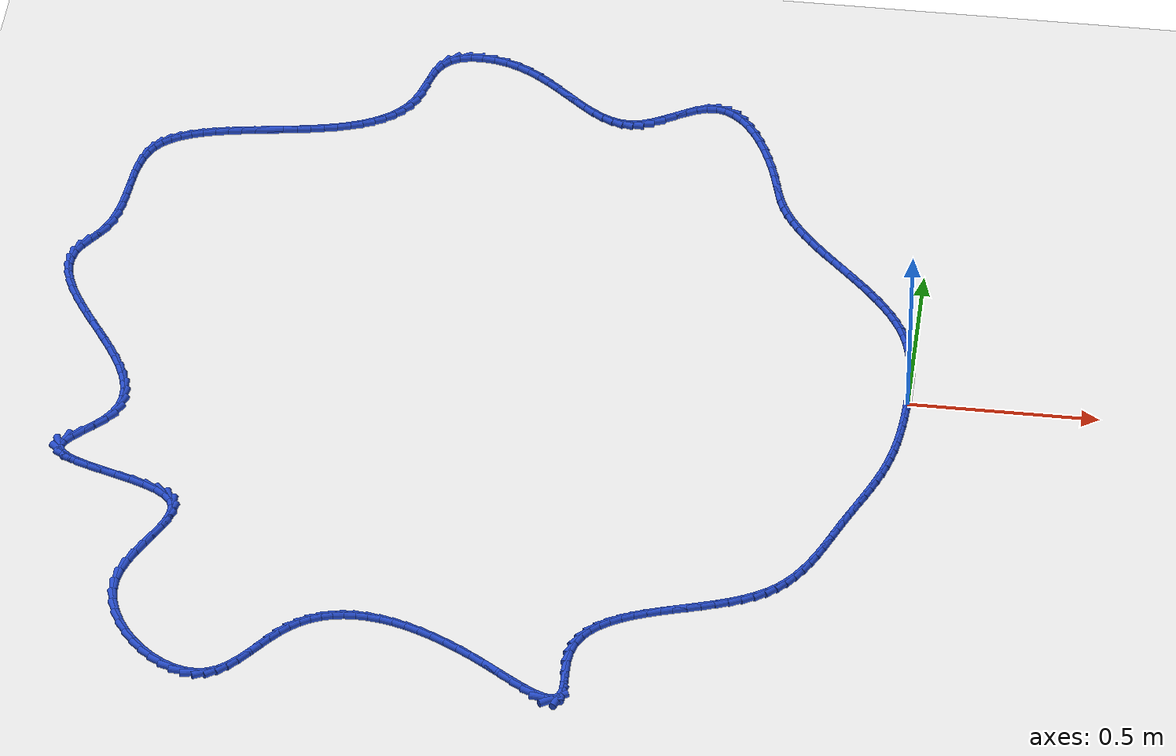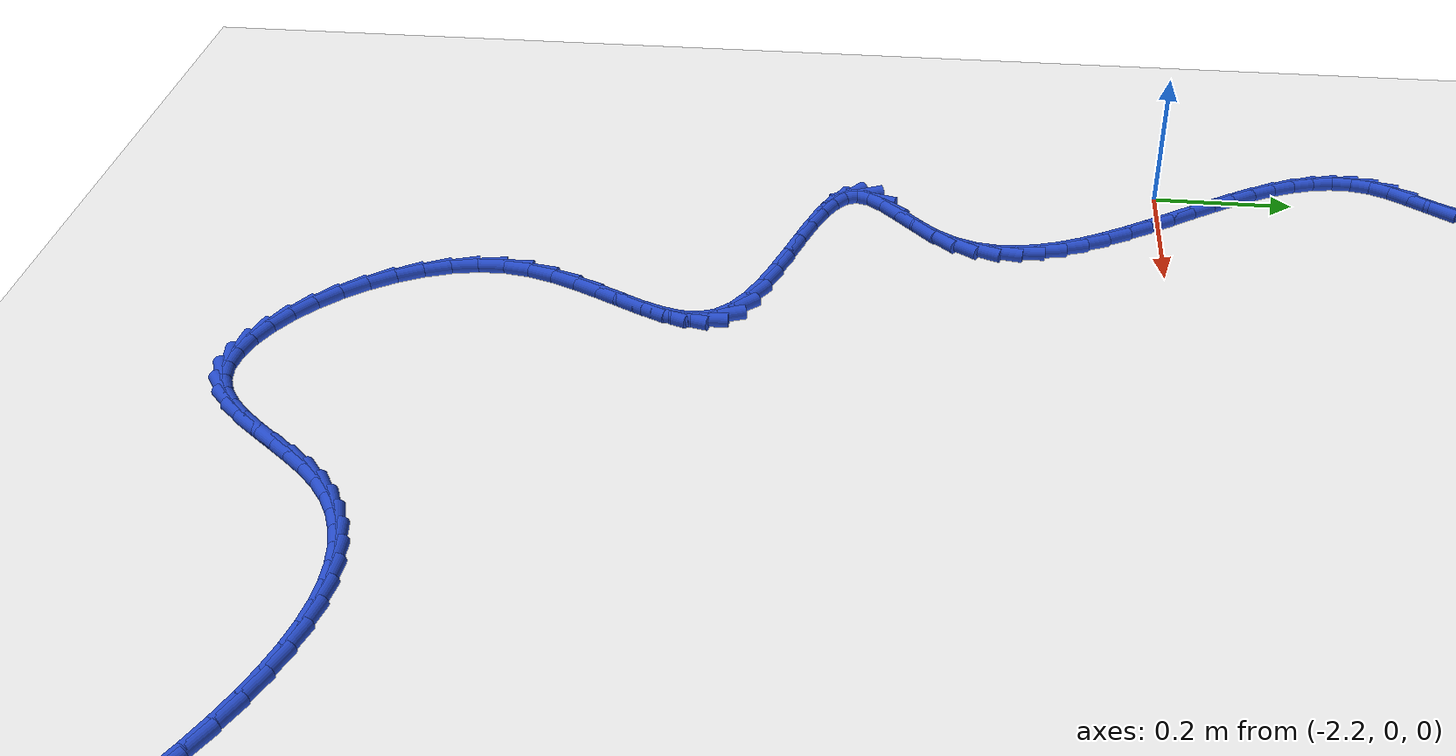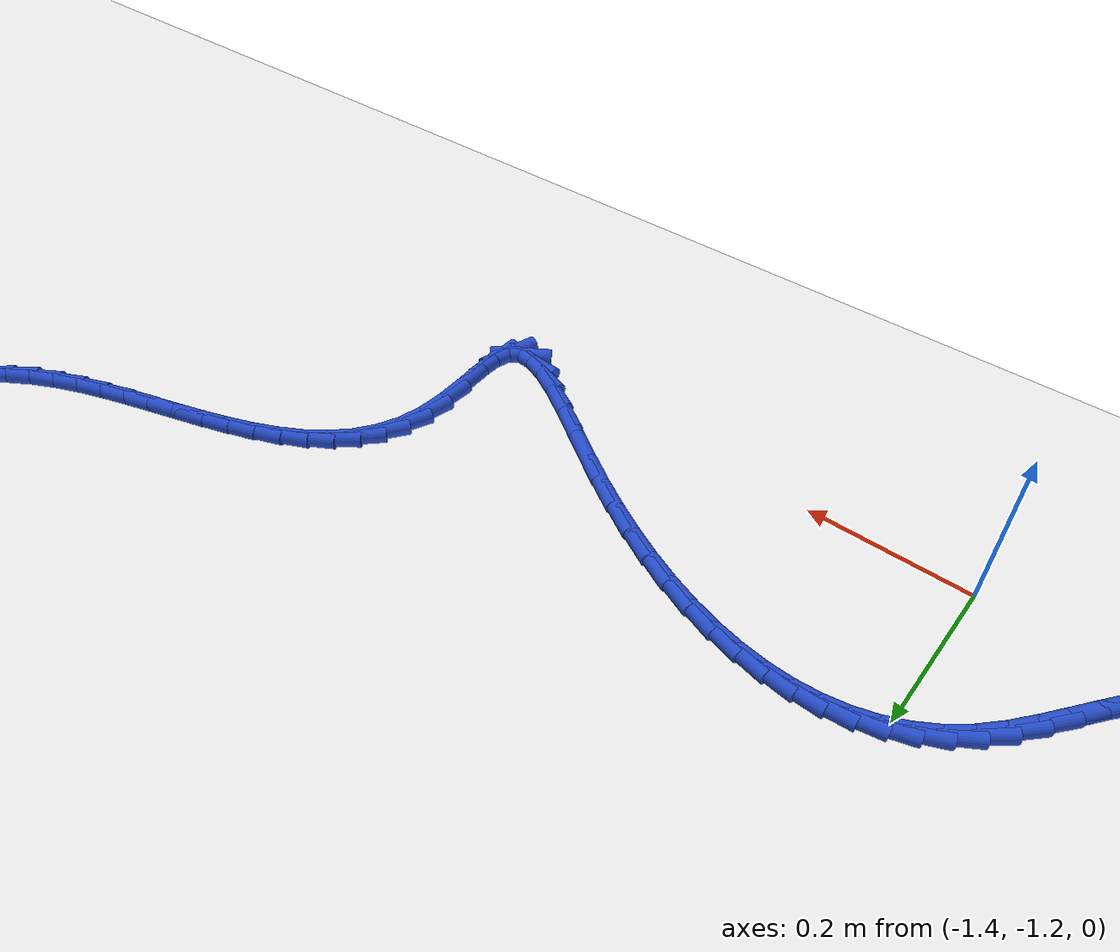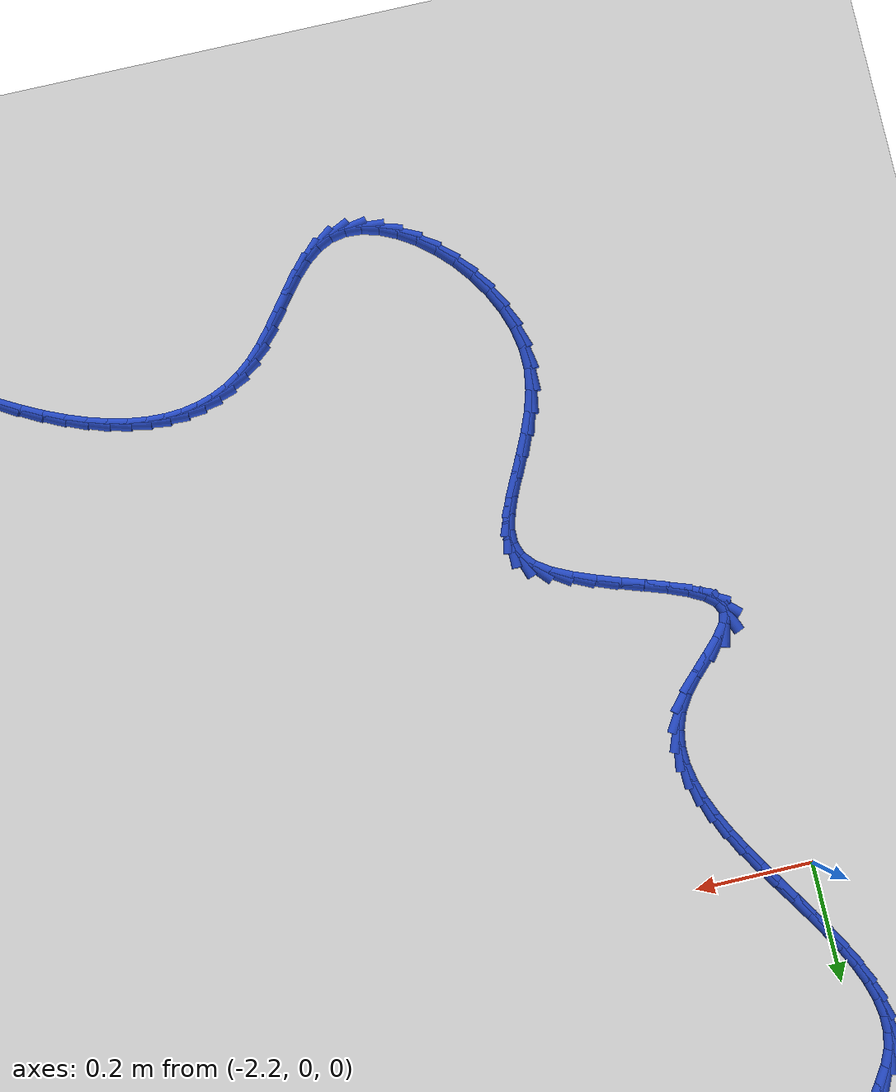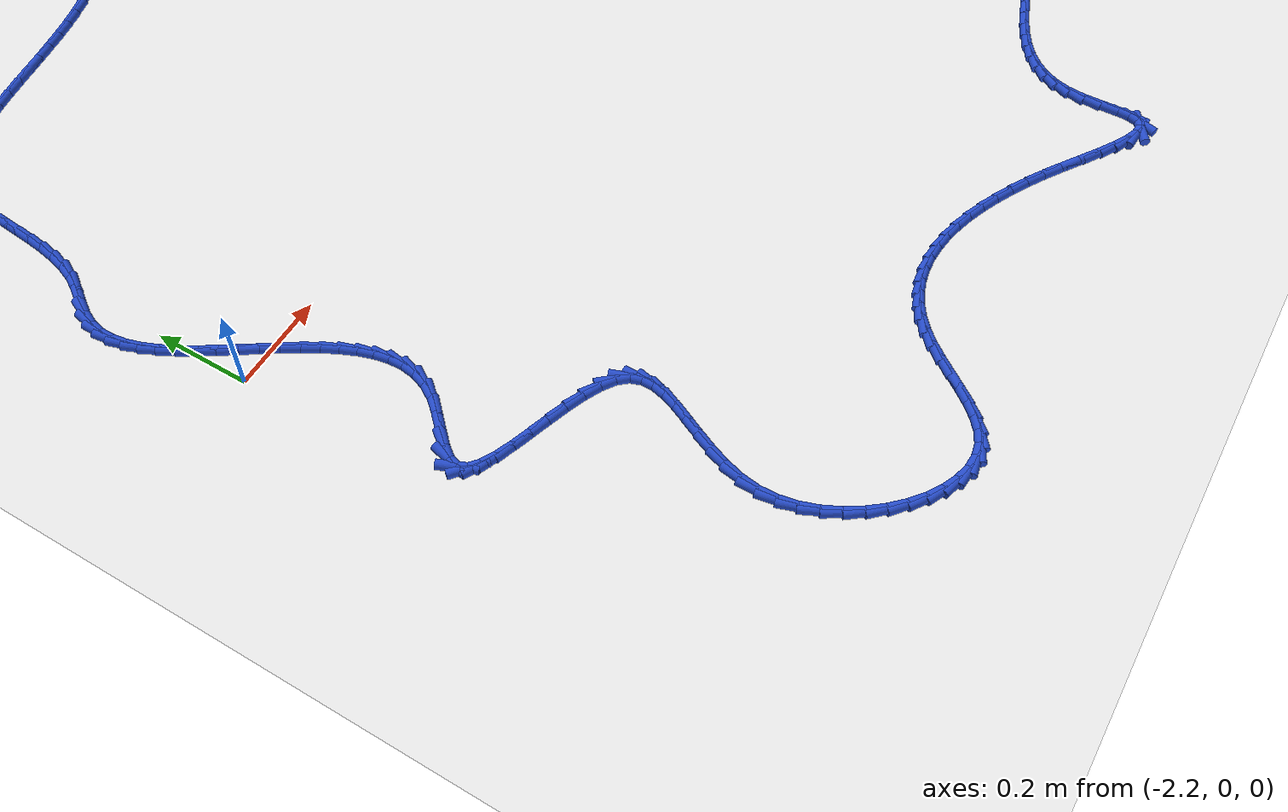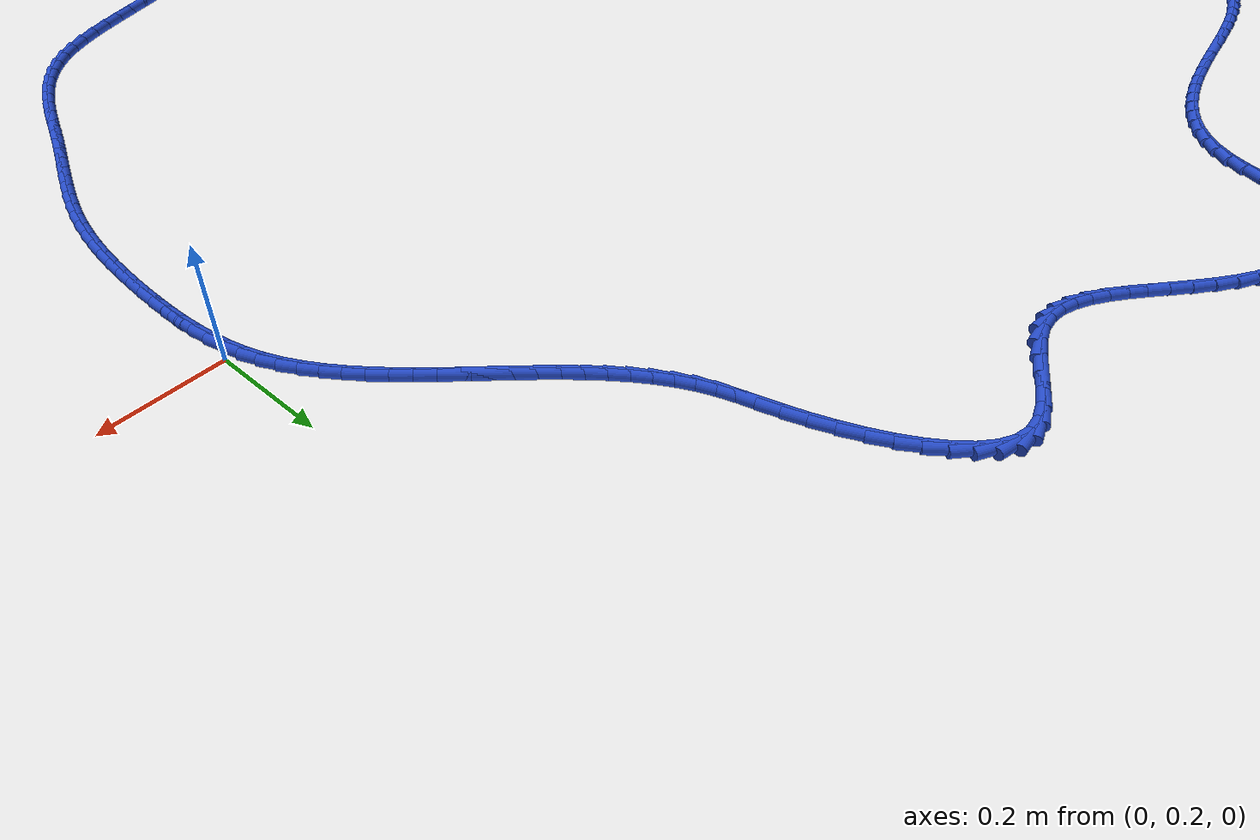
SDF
<sdf version="1.6">
 <world name="default">
  <light name="sun" type="directional">
   <pose>0 0 10 0 -0 0</pose>
   <diffuse>0.8 0.8 0.8 1</diffuse>
   <specular>0.2 0.2 0.2 1</specular>
   <attenuation>
    <range>1000</range>
    <constant>0.9</constant>
    <linear>0.01</linear>
    <quadratic>0.001</quadratic>
   </attenuation>
   <direction>-0.5 0.1 -0.9</direction>
  </light>
  <model name="ground_plane">
   <static>1</static>
   <link name="link">
    <collision name="collision">
     <geometry><plane><normal>0 0 1</normal><size>100 100</size></plane></geometry>
     <surface><friction><ode><mu>100</mu><mu2>50</mu2></ode></friction></surface>
    </collision>
    <visual name="visual">
     <cast_shadows>0</cast_shadows>
     <geometry><plane><normal>0 0 1</normal><size>100 100</size></plane></geometry>
     <material>
      <script><uri>file://media/materials/scripts/gazebo.material</uri><name>Gazebo/WhiteGlow</name></script>
     </material>
    </visual>
   </link>
  </model>
  <gravity>0 0 -9.8</gravity>
  <magnetic_field>6e-06 2.3e-05 -4.2e-05</magnetic_field>
  <atmosphere type="adiabatic"/>
  <physics name="default_physics" default="0" type="ode">
   <max_step_size>0.001</max_step_size>
   <real_time_factor>1</real_time_factor>
   <real_time_update_rate>1000</real_time_update_rate>
  </physics>
  <scene><ambient>0.4 0.4 0.4 1</ambient><background>0.7 0.7 0.7 1</background><shadows>1</shadows></scene>
  <spherical_coordinates>
   <surface_model>EARTH_WGS84</surface_model>
   <latitude_deg>0</latitude_deg>
   <longitude_deg>0</longitude_deg>
   <elevation>0</elevation>
   <heading_deg>0</heading_deg>
  </spherical_coordinates>
  <model name="line">
   <link name="link_0">
    <pose>1.951563910473908e-18 -4.85722573273506e-17 0.01 0 1.57 1.5601422020148101</pose>
    <collision name="collision">
     <geometry><cylinder><radius>0.01</radius><length>0.08</length></cylinder></geometry>
    </collision>
    <visual name="visual">
     <material>
      <script><name>Gazebo/Blue</name><uri>file://media/materials/scripts/gazebo.material</uri></script>
     </material>
     <geometry><cylinder><radius>0.01</radius><length>0.08</length></cylinder></geometry>
    </visual>
   </link>
   <link name="link_1">
    <pose>0.0003457075524983117 0.032447007996455744 0.01 0 1.57 -1.557407941470897</pose>
    <collision name="collision">
     <geometry><cylinder><radius>0.01</radius><length>0.08</length></cylinder></geometry>
    </collision>
    <visual name="visual">
     <material>
      <script><name>Gazebo/Blue</name><uri>file://media/materials/scripts/gazebo.material</uri></script>
     </material>
     <geometry><cylinder><radius>0.01</radius><length>0.08</length></cylinder></geometry>
    </visual>
   </link>
   <link name="link_2">
    <pose>-8.86119410091231e-05 0.06488509012977318 0.01 0 1.57 -1.5258298096238987</pose>
    <collision name="collision">
     <geometry><cylinder><radius>0.01</radius><length>0.08</length></cylinder></geometry>
    </collision>
    <visual name="visual">
     <material>
      <script><name>Gazebo/Blue</name><uri>file://media/materials/scripts/gazebo.material</uri></script>
     </material>
     <geometry><cylinder><radius>0.01</radius><length>0.08</length></cylinder></geometry>
    </visual>
   </link>
   <link name="link_3">
    <pose>-0.0015413717403349356 0.09717090198525248 0.01 0 1.57 -1.486296652616927</pose>
    <collision name="collision">
     <geometry><cylinder><radius>0.01</radius><length>0.08</length></cylinder></geometry>
    </collision>
    <visual name="visual">
     <material>
      <script><name>Gazebo/Blue</name><uri>file://media/materials/scripts/gazebo.material</uri></script>
     </material>
     <geometry><cylinder><radius>0.01</radius><length>0.08</length></cylinder></geometry>
    </visual>
   </link>
   <link name="link_4">
    <pose>-0.004250985105291752 0.12916109914819376 0.01 0 1.57 -1.4383055679510994</pose>
    <collision name="collision">
     <geometry><cylinder><radius>0.01</radius><length>0.08</length></cylinder></geometry>
    </collision>
    <visual name="visual">
     <material>
      <script><name>Gazebo/Blue</name><uri>file://media/materials/scripts/gazebo.material</uri></script>
     </material>
     <geometry><cylinder><radius>0.01</radius><length>0.08</length></cylinder></geometry>
    </visual>
   </link>
   <link name="link_5">
    <pose>-0.008455865295692207 0.16071233720389716 0.01 0 1.57 -1.381337579361241</pose>
    <collision name="collision">
     <geometry><cylinder><radius>0.01</radius><length>0.08</length></cylinder></geometry>
    </collision>
    <visual name="visual">
     <material>
      <script><name>Gazebo/Blue</name><uri>file://media/materials/scripts/gazebo.material</uri></script>
     </material>
     <geometry><cylinder><radius>0.01</radius><length>0.08</length></cylinder></geometry>
    </visual>
   </link>
   <link name="link_6">
    <pose>-0.014394425571348925 0.19168127173766283 0.01 0 1.57 -1.3149608072979624</pose>
    <collision name="collision">
     <geometry><cylinder><radius>0.01</radius><length>0.08</length></cylinder></geometry>
    </collision>
    <visual name="visual">
     <material>
      <script><name>Gazebo/Blue</name><uri>file://media/materials/scripts/gazebo.material</uri></script>
     </material>
     <geometry><cylinder><radius>0.01</radius><length>0.08</length></cylinder></geometry>
    </visual>
   </link>
   <link name="link_7">
    <pose>-0.02230507919207454 0.221924558334791 0.01 0 1.57 -1.2389795612155956</pose>
    <collision name="collision">
     <geometry><cylinder><radius>0.01</radius><length>0.08</length></cylinder></geometry>
    </collision>
    <visual name="visual">
     <material>
      <script><name>Gazebo/Blue</name><uri>file://media/materials/scripts/gazebo.material</uri></script>
     </material>
     <geometry><cylinder><radius>0.01</radius><length>0.08</length></cylinder></geometry>
    </visual>
   </link>
   <link name="link_8">
    <pose>-0.0324261800472538 0.2512988819237568 0.01 0 1.57 -1.157377749378496</pose>
    <collision name="collision">
     <geometry><cylinder><radius>0.01</radius><length>0.08</length></cylinder></geometry>
    </collision>
    <visual name="visual">
     <material>
      <script><name>Gazebo/Blue</name><uri>file://media/materials/scripts/gazebo.material</uri></script>
     </material>
     <geometry><cylinder><radius>0.01</radius><length>0.08</length></cylinder></geometry>
    </visual>
   </link>
   <link name="link_9">
    <pose>-0.04489136149666769 0.2797126843925873 0.01 0 1.57 -1.0823882750565061</pose>
    <collision name="collision">
     <geometry><cylinder><radius>0.01</radius><length>0.08</length></cylinder></geometry>
    </collision>
    <visual name="visual">
     <material>
      <script><name>Gazebo/Blue</name><uri>file://media/materials/scripts/gazebo.material</uri></script>
     </material>
     <geometry><cylinder><radius>0.01</radius><length>0.08</length></cylinder></geometry>
    </visual>
   </link>
   <link name="link_10">
    <pose>-0.05951398409438635 0.30723269890909444 0.01 0 1.57 -1.0167722121956417</pose>
    <collision name="collision">
     <geometry><cylinder><radius>0.01</radius><length>0.08</length></cylinder></geometry>
    </collision>
    <visual name="visual">
     <material>
      <script><name>Gazebo/Blue</name><uri>file://media/materials/scripts/gazebo.material</uri></script>
     </material>
     <geometry><cylinder><radius>0.01</radius><length>0.08</length></cylinder></geometry>
    </visual>
   </link>
   <link name="link_11">
    <pose>-0.07604639247050443 0.33395581508435057 0.01 0 1.57 -0.9606285880004451</pose>
    <collision name="collision">
     <geometry><cylinder><radius>0.01</radius><length>0.08</length></cylinder></geometry>
    </collision>
    <visual name="visual">
     <material>
      <script><name>Gazebo/Blue</name><uri>file://media/materials/scripts/gazebo.material</uri></script>
     </material>
     <geometry><cylinder><radius>0.01</radius><length>0.08</length></cylinder></geometry>
    </visual>
   </link>
   <link name="link_12">
    <pose>-0.09424093125511661 0.3599789225294286 0.01 0 1.57 -0.913738444325812</pose>
    <collision name="collision">
     <geometry><cylinder><radius>0.01</radius><length>0.08</length></cylinder></geometry>
    </collision>
    <visual name="visual">
     <material>
      <script><name>Gazebo/Blue</name><uri>file://media/materials/scripts/gazebo.material</uri></script>
     </material>
     <geometry><cylinder><radius>0.01</radius><length>0.08</length></cylinder></geometry>
    </visual>
   </link>
   <link name="link_13">
    <pose>-0.11384994507831754 0.38539891085540084 0.01 0 1.57 -0.8757177984947657</pose>
    <collision name="collision">
     <geometry><cylinder><radius>0.01</radius><length>0.08</length></cylinder></geometry>
    </collision>
    <visual name="visual">
     <material>
      <script><name>Gazebo/Blue</name><uri>file://media/materials/scripts/gazebo.material</uri></script>
     </material>
     <geometry><cylinder><radius>0.01</radius><length>0.08</length></cylinder></geometry>
    </visual>
   </link>
   <link name="link_14">
    <pose>-0.1346257785702018 0.41031266967334 0.01 0 1.57 -0.8461341198908823</pose>
    <collision name="collision">
     <geometry><cylinder><radius>0.01</radius><length>0.08</length></cylinder></geometry>
    </collision>
    <visual name="visual">
     <material>
      <script><name>Gazebo/Blue</name><uri>file://media/materials/scripts/gazebo.material</uri></script>
     </material>
     <geometry><cylinder><radius>0.01</radius><length>0.08</length></cylinder></geometry>
    </visual>
   </link>
   <link name="link_15">
    <pose>-0.15632077636086408 0.43481708859431834 0.01 0 1.57 -0.8245860310999504</pose>
    <collision name="collision">
     <geometry><cylinder><radius>0.01</radius><length>0.08</length></cylinder></geometry>
    </collision>
    <visual name="visual">
     <material>
      <script><name>Gazebo/Blue</name><uri>file://media/materials/scripts/gazebo.material</uri></script>
     </material>
     <geometry><cylinder><radius>0.01</radius><length>0.08</length></cylinder></geometry>
    </visual>
   </link>
   <link name="link_16">
    <pose>-0.17868728308039913 0.4590090572294087 0.01 0 1.57 -0.8107536357878705</pose>
    <collision name="collision">
     <geometry><cylinder><radius>0.01</radius><length>0.08</length></cylinder></geometry>
    </collision>
    <visual name="visual">
     <material>
      <script><name>Gazebo/Blue</name><uri>file://media/materials/scripts/gazebo.material</uri></script>
     </material>
     <geometry><cylinder><radius>0.01</radius><length>0.08</length></cylinder></geometry>
    </visual>
   </link>
   <link name="link_17">
    <pose>-0.20147764335890142 0.4829854651896833 0.01 0 1.57 -0.8044282596533969</pose>
    <collision name="collision">
     <geometry><cylinder><radius>0.01</radius><length>0.08</length></cylinder></geometry>
    </collision>
    <visual name="visual">
     <material>
      <script><name>Gazebo/Blue</name><uri>file://media/materials/scripts/gazebo.material</uri></script>
     </material>
     <geometry><cylinder><radius>0.01</radius><length>0.08</length></cylinder></geometry>
    </visual>
   </link>
   <link name="link_18">
    <pose>-0.22444420182646577 0.5068432020862151 0.01 0 1.57 -0.8055288244147857</pose>
    <collision name="collision">
     <geometry><cylinder><radius>0.01</radius><length>0.08</length></cylinder></geometry>
    </collision>
    <visual name="visual">
     <material>
      <script><name>Gazebo/Blue</name><uri>file://media/materials/scripts/gazebo.material</uri></script>
     </material>
     <geometry><cylinder><radius>0.01</radius><length>0.08</length></cylinder></geometry>
    </visual>
   </link>
   <link name="link_19">
    <pose>-0.24733930311318658 0.5306791575300762 0.01 0 1.57 -0.8141095556093366</pose>
    <collision name="collision">
     <geometry><cylinder><radius>0.01</radius><length>0.08</length></cylinder></geometry>
    </collision>
    <visual name="visual">
     <material>
      <script><name>Gazebo/Blue</name><uri>file://media/materials/scripts/gazebo.material</uri></script>
     </material>
     <geometry><cylinder><radius>0.01</radius><length>0.08</length></cylinder></geometry>
    </visual>
   </link>
   <link name="link_20">
    <pose>-0.2699152918491588 0.5545902211323395 0.01 0 1.57 -0.8303610668236875</pose>
    <collision name="collision">
     <geometry><cylinder><radius>0.01</radius><length>0.08</length></cylinder></geometry>
    </collision>
    <visual name="visual">
     <material>
      <script><name>Gazebo/Blue</name><uri>file://media/materials/scripts/gazebo.material</uri></script>
     </material>
     <geometry><cylinder><radius>0.01</radius><length>0.08</length></cylinder></geometry>
    </visual>
   </link>
   <link name="link_21">
    <pose>-0.2919245126644769 0.5786732825040772 0.01 0 1.57 -0.8546041882099095</pose>
    <collision name="collision">
     <geometry><cylinder><radius>0.01</radius><length>0.08</length></cylinder></geometry>
    </collision>
    <visual name="visual">
     <material>
      <script><name>Gazebo/Blue</name><uri>file://media/materials/scripts/gazebo.material</uri></script>
     </material>
     <geometry><cylinder><radius>0.01</radius><length>0.08</length></cylinder></geometry>
    </visual>
   </link>
   <link name="link_22">
    <pose>-0.31311931018923544 0.6030252312563621 0.01 0 1.57 -0.8872730525588548</pose>
    <collision name="collision">
     <geometry><cylinder><radius>0.01</radius><length>0.08</length></cylinder></geometry>
    </collision>
    <visual name="visual">
     <material>
      <script><name>Gazebo/Blue</name><uri>file://media/materials/scripts/gazebo.material</uri></script>
     </material>
     <geometry><cylinder><radius>0.01</radius><length>0.08</length></cylinder></geometry>
    </visual>
   </link>
   <link name="link_23">
    <pose>-0.3332520290535294 0.6277429570002668 0.01 0 1.57 -0.9288807938306439</pose>
    <collision name="collision">
     <geometry><cylinder><radius>0.01</radius><length>0.08</length></cylinder></geometry>
    </collision>
    <visual name="visual">
     <material>
      <script><name>Gazebo/Blue</name><uri>file://media/materials/scripts/gazebo.material</uri></script>
     </material>
     <geometry><cylinder><radius>0.01</radius><length>0.08</length></cylinder></geometry>
    </visual>
   </link>
   <link name="link_24">
    <pose>-0.3520750138874532 0.6529233493468637 0.01 0 1.57 -0.9799580597882548</pose>
    <collision name="collision">
     <geometry><cylinder><radius>0.01</radius><length>0.08</length></cylinder></geometry>
    </collision>
    <visual name="visual">
     <material>
      <script><name>Gazebo/Blue</name><uri>file://media/materials/scripts/gazebo.material</uri></script>
     </material>
     <geometry><cylinder><radius>0.01</radius><length>0.08</length></cylinder></geometry>
    </visual>
   </link>
   <link name="link_25">
    <pose>-0.36934060932110147 0.6786632979072252 0.01 0 1.57 -1.0409527470167534</pose>
    <collision name="collision">
     <geometry><cylinder><radius>0.01</radius><length>0.08</length></cylinder></geometry>
    </collision>
    <visual name="visual">
     <material>
      <script><name>Gazebo/Blue</name><uri>file://media/materials/scripts/gazebo.material</uri></script>
     </material>
     <geometry><cylinder><radius>0.01</radius><length>0.08</length></cylinder></geometry>
    </visual>
   </link>
   <link name="link_26">
    <pose>-0.3848011599845688 0.705059692292424 0.01 0 1.57 -1.1120821003731851</pose>
    <collision name="collision">
     <geometry><cylinder><radius>0.01</radius><length>0.08</length></cylinder></geometry>
    </collision>
    <visual name="visual">
     <material>
      <script><name>Gazebo/Blue</name><uri>file://media/materials/scripts/gazebo.material</uri></script>
     </material>
     <geometry><cylinder><radius>0.01</radius><length>0.08</length></cylinder></geometry>
    </visual>
   </link>
   <link name="link_27">
    <pose>-0.3982090105079501 0.7322094221135328 0.01 0 1.57 -1.1930303214714388</pose>
    <collision name="collision">
     <geometry><cylinder><radius>0.01</radius><length>0.08</length></cylinder></geometry>
    </collision>
    <visual name="visual">
     <material>
      <script><name>Gazebo/Blue</name><uri>file://media/materials/scripts/gazebo.material</uri></script>
     </material>
     <geometry><cylinder><radius>0.01</radius><length>0.08</length></cylinder></geometry>
    </visual>
   </link>
   <link name="link_28">
    <pose>-0.4093203415947308 0.7602100297532666 0.01 0 1.57 -1.2680264631497355</pose>
    <collision name="collision">
     <geometry><cylinder><radius>0.01</radius><length>0.08</length></cylinder></geometry>
    </collision>
    <visual name="visual">
     <material>
      <script><name>Gazebo/Blue</name><uri>file://media/materials/scripts/gazebo.material</uri></script>
     </material>
     <geometry><cylinder><radius>0.01</radius><length>0.08</length></cylinder></geometry>
    </visual>
   </link>
   <link name="link_29">
    <pose>-0.4183897522445403 0.7892438717511238 0.01 0 1.57 -1.3053573788301964</pose>
    <collision name="collision">
     <geometry><cylinder><radius>0.01</radius><length>0.08</length></cylinder></geometry>
    </collision>
    <visual name="visual">
     <material>
      <script><name>Gazebo/Blue</name><uri>file://media/materials/scripts/gazebo.material</uri></script>
     </material>
     <geometry><cylinder><radius>0.01</radius><length>0.08</length></cylinder></geometry>
    </visual>
   </link>
   <link name="link_30">
    <pose>-0.42665883700440327 0.8196612583428206 0.01 0 1.57 -1.3030247935200012</pose>
    <collision name="collision">
     <geometry><cylinder><radius>0.01</radius><length>0.08</length></cylinder></geometry>
    </collision>
    <visual name="visual">
     <material>
      <script><name>Gazebo/Blue</name><uri>file://media/materials/scripts/gazebo.material</uri></script>
     </material>
     <geometry><cylinder><radius>0.01</radius><length>0.08</length></cylinder></geometry>
    </visual>
   </link>
   <link name="link_31">
    <pose>-0.435485286380873 0.8518322554210984 0.01 0 1.57 -1.2708169113477539</pose>
    <collision name="collision">
     <geometry><cylinder><radius>0.01</radius><length>0.08</length></cylinder></geometry>
    </collision>
    <visual name="visual">
     <material>
      <script><name>Gazebo/Blue</name><uri>file://media/materials/scripts/gazebo.material</uri></script>
     </material>
     <geometry><cylinder><radius>0.01</radius><length>0.08</length></cylinder></geometry>
    </visual>
   </link>
   <link name="link_32">
    <pose>-0.44603187365033814 0.8859289909467123 0.01 0 1.57 -1.2302124233695544</pose>
    <collision name="collision">
     <geometry><cylinder><radius>0.01</radius><length>0.08</length></cylinder></geometry>
    </collision>
    <visual name="visual">
     <material>
      <script><name>Gazebo/Blue</name><uri>file://media/materials/scripts/gazebo.material</uri></script>
     </material>
     <geometry><cylinder><radius>0.01</radius><length>0.08</length></cylinder></geometry>
    </visual>
   </link>
   <link name="link_33">
    <pose>-0.45852036859303313 0.9211680063175332 0.01 0 1.57 -1.1843315811143795</pose>
    <collision name="collision">
     <geometry><cylinder><radius>0.01</radius><length>0.08</length></cylinder></geometry>
    </collision>
    <visual name="visual">
     <material>
      <script><name>Gazebo/Blue</name><uri>file://media/materials/scripts/gazebo.material</uri></script>
     </material>
     <geometry><cylinder><radius>0.01</radius><length>0.08</length></cylinder></geometry>
    </visual>
   </link>
   <link name="link_34">
    <pose>-0.47288894350812166 0.9564778504390685 0.01 0 1.57 -1.1299691437176658</pose>
    <collision name="collision">
     <geometry><cylinder><radius>0.01</radius><length>0.08</length></cylinder></geometry>
    </collision>
    <visual name="visual">
     <material>
      <script><name>Gazebo/Blue</name><uri>file://media/materials/scripts/gazebo.material</uri></script>
     </material>
     <geometry><cylinder><radius>0.01</radius><length>0.08</length></cylinder></geometry>
    </visual>
   </link>
   <link name="link_35">
    <pose>-0.4890757127902467 0.9907870134149392 0.01 0 1.57 -1.0629005494111992</pose>
    <collision name="collision">
     <geometry><cylinder><radius>0.01</radius><length>0.08</length></cylinder></geometry>
    </collision>
    <visual name="visual">
     <material>
      <script><name>Gazebo/Blue</name><uri>file://media/materials/scripts/gazebo.material</uri></script>
     </material>
     <geometry><cylinder><radius>0.01</radius><length>0.08</length></cylinder></geometry>
    </visual>
   </link>
   <link name="link_36">
    <pose>-0.5070187908340514 1.0230239853487653 0.01 0 1.57 -0.9770574449020017</pose>
    <collision name="collision">
     <geometry><cylinder><radius>0.01</radius><length>0.08</length></cylinder></geometry>
    </collision>
    <visual name="visual">
     <material>
      <script><name>Gazebo/Blue</name><uri>file://media/materials/scripts/gazebo.material</uri></script>
     </material>
     <geometry><cylinder><radius>0.01</radius><length>0.08</length></cylinder></geometry>
    </visual>
   </link>
   <link name="link_37">
    <pose>-0.5266562920341785 1.052117256344167 0.01 0 1.57 -0.8634229747746909</pose>
    <collision name="collision">
     <geometry><cylinder><radius>0.01</radius><length>0.08</length></cylinder></geometry>
    </collision>
    <visual name="visual">
     <material>
      <script><name>Gazebo/Blue</name><uri>file://media/materials/scripts/gazebo.material</uri></script>
     </material>
     <geometry><cylinder><radius>0.01</radius><length>0.08</length></cylinder></geometry>
    </visual>
   </link>
   <link name="link_38">
    <pose>-0.5479263307852714 1.0769953165047652 0.01 0 1.57 -0.7089695329008289</pose>
    <collision name="collision">
     <geometry><cylinder><radius>0.01</radius><length>0.08</length></cylinder></geometry>
    </collision>
    <visual name="visual">
     <material>
      <script><name>Gazebo/Blue</name><uri>file://media/materials/scripts/gazebo.material</uri></script>
     </material>
     <geometry><cylinder><radius>0.01</radius><length>0.08</length></cylinder></geometry>
    </visual>
   </link>
   <link name="link_39">
    <pose>-0.570767021481973 1.0965866559341801 0.01 0 1.57 -0.49781308248723494</pose>
    <collision name="collision">
     <geometry><cylinder><radius>0.01</radius><length>0.08</length></cylinder></geometry>
    </collision>
    <visual name="visual">
     <material>
      <script><name>Gazebo/Blue</name><uri>file://media/materials/scripts/gazebo.material</uri></script>
     </material>
     <geometry><cylinder><radius>0.01</radius><length>0.08</length></cylinder></geometry>
    </visual>
   </link>
   <link name="link_40">
    <pose>-0.5951164785189262 1.1098197647360317 0.01 0 1.57 -0.22128463945847898</pose>
    <collision name="collision">
     <geometry><cylinder><radius>0.01</radius><length>0.08</length></cylinder></geometry>
    </collision>
    <visual name="visual">
     <material>
      <script><name>Gazebo/Blue</name><uri>file://media/materials/scripts/gazebo.material</uri></script>
     </material>
     <geometry><cylinder><radius>0.01</radius><length>0.08</length></cylinder></geometry>
    </visual>
   </link>
   <link name="link_41">
    <pose>-0.6209128162907744 1.115623133013941 0.01 0 1.57 0.09308619022920465</pose>
    <collision name="collision">
     <geometry><cylinder><radius>0.01</radius><length>0.08</length></cylinder></geometry>
    </collision>
    <visual name="visual">
     <material>
      <script><name>Gazebo/Blue</name><uri>file://media/materials/scripts/gazebo.material</uri></script>
     </material>
     <geometry><cylinder><radius>0.01</radius><length>0.08</length></cylinder></geometry>
    </visual>
   </link>
   <link name="link_42">
    <pose>-0.6480802191490858 1.1130868932094247 0.01 0 1.57 0.33399810236683</pose>
    <collision name="collision">
     <geometry><cylinder><radius>0.01</radius><length>0.08</length></cylinder></geometry>
    </collision>
    <visual name="visual">
     <material>
      <script><name>Gazebo/Blue</name><uri>file://media/materials/scripts/gazebo.material</uri></script>
     </material>
     <geometry><cylinder><radius>0.01</radius><length>0.08</length></cylinder></geometry>
    </visual>
   </link>
   <link name="link_43">
    <pose>-0.6763732659363002 1.1032692571783274 0.01 0 1.57 0.4690690829159068</pose>
    <collision name="collision">
     <geometry><cylinder><radius>0.01</radius><length>0.08</length></cylinder></geometry>
    </collision>
    <visual name="visual">
     <material>
      <script><name>Gazebo/Blue</name><uri>file://media/materials/scripts/gazebo.material</uri></script>
     </material>
     <geometry><cylinder><radius>0.01</radius><length>0.08</length></cylinder></geometry>
    </visual>
   </link>
   <link name="link_44">
    <pose>-0.7054333575391408 1.0885417384843585 0.01 0 1.57 0.5294199195136121</pose>
    <collision name="collision">
     <geometry><cylinder><radius>0.01</radius><length>0.08</length></cylinder></geometry>
    </collision>
    <visual name="visual">
     <material>
      <script><name>Gazebo/Blue</name><uri>file://media/materials/scripts/gazebo.material</uri></script>
     </material>
     <geometry><cylinder><radius>0.01</radius><length>0.08</length></cylinder></geometry>
    </visual>
   </link>
   <link name="link_45">
    <pose>-0.7348998324313784 1.0712997826525015 0.01 0 1.57 0.5317450055895862</pose>
    <collision name="collision">
     <geometry><cylinder><radius>0.01</radius><length>0.08</length></cylinder></geometry>
    </collision>
    <visual name="visual">
     <material>
      <script><name>Gazebo/Blue</name><uri>file://media/materials/scripts/gazebo.material</uri></script>
     </material>
     <geometry><cylinder><radius>0.01</radius><length>0.08</length></cylinder></geometry>
    </visual>
   </link>
   <link name="link_46">
    <pose>-0.7644120290867827 1.0539388352077395 0.01 0 1.57 0.47687143395210596</pose>
    <collision name="collision">
     <geometry><cylinder><radius>0.01</radius><length>0.08</length></cylinder></geometry>
    </collision>
    <visual name="visual">
     <material>
      <script><name>Gazebo/Blue</name><uri>file://media/materials/scripts/gazebo.material</uri></script>
     </material>
     <geometry><cylinder><radius>0.01</radius><length>0.08</length></cylinder></geometry>
    </visual>
   </link>
   <link name="link_47">
    <pose>-0.7936092859791244 1.038854341675056 0.01 0 1.57 0.3500426043366987</pose>
    <collision name="collision">
     <geometry><cylinder><radius>0.01</radius><length>0.08</length></cylinder></geometry>
    </collision>
    <visual name="visual">
     <material>
      <script><name>Gazebo/Blue</name><uri>file://media/materials/scripts/gazebo.material</uri></script>
     </material>
     <geometry><cylinder><radius>0.01</radius><length>0.08</length></cylinder></geometry>
    </visual>
   </link>
   <link name="link_48">
    <pose>-0.8221309415821738 1.0284417475794352 0.01 0 1.57 0.13979342879848258</pose>
    <collision name="collision">
     <geometry><cylinder><radius>0.01</radius><length>0.08</length></cylinder></geometry>
    </collision>
    <visual name="visual">
     <material>
      <script><name>Gazebo/Blue</name><uri>file://media/materials/scripts/gazebo.material</uri></script>
     </material>
     <geometry><cylinder><radius>0.01</radius><length>0.08</length></cylinder></geometry>
    </visual>
   </link>
   <link name="link_49">
    <pose>-0.8497121146427964 1.0245607668585095 0.01 0 1.57 -0.08808241440504086</pose>
    <collision name="collision">
     <geometry><cylinder><radius>0.01</radius><length>0.08</length></cylinder></geometry>
    </collision>
    <visual name="visual">
     <material>
      <script><name>Gazebo/Blue</name><uri>file://media/materials/scripts/gazebo.material</uri></script>
     </material>
     <geometry><cylinder><radius>0.01</radius><length>0.08</length></cylinder></geometry>
    </visual>
   </link>
   <link name="link_50">
    <pose>-0.8764718043731252 1.0269239396701266 0.01 0 1.57 -0.2892102116565944</pose>
    <collision name="collision">
     <geometry><cylinder><radius>0.01</radius><length>0.08</length></cylinder></geometry>
    </collision>
    <visual name="visual">
     <material>
      <script><name>Gazebo/Blue</name><uri>file://media/materials/scripts/gazebo.material</uri></script>
     </material>
     <geometry><cylinder><radius>0.01</radius><length>0.08</length></cylinder></geometry>
    </visual>
   </link>
   <link name="link_51">
    <pose>-0.9026251703209627 1.0347059487657628 0.01 0 1.57 -0.44782504012098623</pose>
    <collision name="collision">
     <geometry><cylinder><radius>0.01</radius><length>0.08</length></cylinder></geometry>
    </collision>
    <visual name="visual">
     <material>
      <script><name>Gazebo/Blue</name><uri>file://media/materials/scripts/gazebo.material</uri></script>
     </material>
     <geometry><cylinder><radius>0.01</radius><length>0.08</length></cylinder></geometry>
    </visual>
   </link>
   <link name="link_52">
    <pose>-0.9283873720341391 1.047081476896741 0.01 0 1.57 -0.5628698537850142</pose>
    <collision name="collision">
     <geometry><cylinder><radius>0.01</radius><length>0.08</length></cylinder></geometry>
    </collision>
    <visual name="visual">
     <material>
      <script><name>Gazebo/Blue</name><uri>file://media/materials/scripts/gazebo.material</uri></script>
     </material>
     <geometry><cylinder><radius>0.01</radius><length>0.08</length></cylinder></geometry>
    </visual>
   </link>
   <link name="link_53">
    <pose>-0.9539735690604847 1.0632252068143828 0.01 0 1.57 -0.6401861879559722</pose>
    <collision name="collision">
     <geometry><cylinder><radius>0.01</radius><length>0.08</length></cylinder></geometry>
    </collision>
    <visual name="visual">
     <material>
      <script><name>Gazebo/Blue</name><uri>file://media/materials/scripts/gazebo.material</uri></script>
     </material>
     <geometry><cylinder><radius>0.01</radius><length>0.08</length></cylinder></geometry>
    </visual>
   </link>
   <link name="link_54">
    <pose>-0.9795989209478297 1.082311821270011 0.01 0 1.57 -0.6864213990536095</pose>
    <collision name="collision">
     <geometry><cylinder><radius>0.01</radius><length>0.08</length></cylinder></geometry>
    </collision>
    <visual name="visual">
     <material>
      <script><name>Gazebo/Blue</name><uri>file://media/materials/scripts/gazebo.material</uri></script>
     </material>
     <geometry><cylinder><radius>0.01</radius><length>0.08</length></cylinder></geometry>
    </visual>
   </link>
   <link name="link_55">
    <pose>-1.0054785872440042 1.1035160030149485 0.01 0 1.57 -0.7066858386909407</pose>
    <collision name="collision">
     <geometry><cylinder><radius>0.01</radius><length>0.08</length></cylinder></geometry>
    </collision>
    <visual name="visual">
     <material>
      <script><name>Gazebo/Blue</name><uri>file://media/materials/scripts/gazebo.material</uri></script>
     </material>
     <geometry><cylinder><radius>0.01</radius><length>0.08</length></cylinder></geometry>
    </visual>
   </link>
   <link name="link_56">
    <pose>-1.0318277274968386 1.1260124348005174 0.01 0 1.57 -0.7041644778268977</pose>
    <collision name="collision">
     <geometry><cylinder><radius>0.01</radius><length>0.08</length></cylinder></geometry>
    </collision>
    <visual name="visual">
     <material>
      <script><name>Gazebo/Blue</name><uri>file://media/materials/scripts/gazebo.material</uri></script>
     </material>
     <geometry><cylinder><radius>0.01</radius><length>0.08</length></cylinder></geometry>
    </visual>
   </link>
   <link name="link_57">
    <pose>-1.0588615012541631 1.1489757993780398 0.01 0 1.57 -0.6803501926245025</pose>
    <collision name="collision">
     <geometry><cylinder><radius>0.01</radius><length>0.08</length></cylinder></geometry>
    </collision>
    <visual name="visual">
     <material>
      <script><name>Gazebo/Blue</name><uri>file://media/materials/scripts/gazebo.material</uri></script>
     </material>
     <geometry><cylinder><radius>0.01</radius><length>0.08</length></cylinder></geometry>
    </visual>
   </link>
   <link name="link_58">
    <pose>-1.0867950680638074 1.1715807794988387 0.01 0 1.57 -0.6354082927952933</pose>
    <collision name="collision">
     <geometry><cylinder><radius>0.01</radius><length>0.08</length></cylinder></geometry>
    </collision>
    <visual name="visual">
     <material>
      <script><name>Gazebo/Blue</name><uri>file://media/materials/scripts/gazebo.material</uri></script>
     </material>
     <geometry><cylinder><radius>0.01</radius><length>0.08</length></cylinder></geometry>
    </visual>
   </link>
   <link name="link_59">
    <pose>-1.1158435874736021 1.1930020579142362 0.01 0 1.57 -0.5686107847823842</pose>
    <collision name="collision">
     <geometry><cylinder><radius>0.01</radius><length>0.08</length></cylinder></geometry>
    </collision>
    <visual name="visual">
     <material>
      <script><name>Gazebo/Blue</name><uri>file://media/materials/scripts/gazebo.material</uri></script>
     </material>
     <geometry><cylinder><radius>0.01</radius><length>0.08</length></cylinder></geometry>
    </visual>
   </link>
   <link name="link_60">
    <pose>-1.1462222190313773 1.2124143173755546 0.01 0 1.57 -0.47896418652722533</pose>
    <collision name="collision">
     <geometry><cylinder><radius>0.01</radius><length>0.08</length></cylinder></geometry>
    </collision>
    <visual name="visual">
     <material>
      <script><name>Gazebo/Blue</name><uri>file://media/materials/scripts/gazebo.material</uri></script>
     </material>
     <geometry><cylinder><radius>0.01</radius><length>0.08</length></cylinder></geometry>
    </visual>
   </link>
   <link name="link_61">
    <pose>-1.1781461222849632 1.2289922406341167 0.01 0 1.57 -0.3662326528747795</pose>
    <collision name="collision">
     <geometry><cylinder><radius>0.01</radius><length>0.08</length></cylinder></geometry>
    </collision>
    <visual name="visual">
     <material>
      <script><name>Gazebo/Blue</name><uri>file://media/materials/scripts/gazebo.material</uri></script>
     </material>
     <geometry><cylinder><radius>0.01</radius><length>0.08</length></cylinder></geometry>
    </visual>
   </link>
   <link name="link_62">
    <pose>-1.2118288288986172 1.2419107498552322 0.01 0 1.57 -0.23743243432189245</pose>
    <collision name="collision">
     <geometry><cylinder><radius>0.01</radius><length>0.08</length></cylinder></geometry>
    </collision>
    <visual name="visual">
     <material>
      <script><name>Gazebo/Blue</name><uri>file://media/materials/scripts/gazebo.material</uri></script>
     </material>
     <geometry><cylinder><radius>0.01</radius><length>0.08</length></cylinder></geometry>
    </visual>
   </link>
   <link name="link_63">
    <pose>-1.2469842184208553 1.25041825139395 0.01 0 1.57 -0.09988791679510114</pose>
    <collision name="collision">
     <geometry><cylinder><radius>0.01</radius><length>0.08</length></cylinder></geometry>
    </collision>
    <visual name="visual">
     <material>
      <script><name>Gazebo/Blue</name><uri>file://media/materials/scripts/gazebo.material</uri></script>
     </material>
     <geometry><cylinder><radius>0.01</radius><length>0.08</length></cylinder></geometry>
    </visual>
   </link>
   <link name="link_64">
    <pose>-1.2821237734833864 1.253939988969543 0.01 0 1.57 0.060084258238647714</pose>
    <collision name="collision">
     <geometry><cylinder><radius>0.01</radius><length>0.08</length></cylinder></geometry>
    </collision>
    <visual name="visual">
     <material>
      <script><name>Gazebo/Blue</name><uri>file://media/materials/scripts/gazebo.material</uri></script>
     </material>
     <geometry><cylinder><radius>0.01</radius><length>0.08</length></cylinder></geometry>
    </visual>
   </link>
   <link name="link_65">
    <pose>-1.3155817790789972 1.2519272668832555 0.01 0 1.57 0.2626583918782028</pose>
    <collision name="collision">
     <geometry><cylinder><radius>0.01</radius><length>0.08</length></cylinder></geometry>
    </collision>
    <visual name="visual">
     <material>
      <script><name>Gazebo/Blue</name><uri>file://media/materials/scripts/gazebo.material</uri></script>
     </material>
     <geometry><cylinder><radius>0.01</radius><length>0.08</length></cylinder></geometry>
    </visual>
   </link>
   <link name="link_66">
    <pose>-1.345692520200476 1.2438313894363324 0.01 0 1.57 0.5306678028779322</pose>
    <collision name="collision">
     <geometry><cylinder><radius>0.01</radius><length>0.08</length></cylinder></geometry>
    </collision>
    <visual name="visual">
     <material>
      <script><name>Gazebo/Blue</name><uri>file://media/materials/scripts/gazebo.material</uri></script>
     </material>
     <geometry><cylinder><radius>0.01</radius><length>0.08</length></cylinder></geometry>
    </visual>
   </link>
   <link name="link_67">
    <pose>-1.3707902818406101 1.2291036609300183 0.01 0 1.57 0.8563380506973972</pose>
    <collision name="collision">
     <geometry><cylinder><radius>0.01</radius><length>0.08</length></cylinder></geometry>
    </collision>
    <visual name="visual">
     <material>
      <script><name>Gazebo/Blue</name><uri>file://media/materials/scripts/gazebo.material</uri></script>
     </material>
     <geometry><cylinder><radius>0.01</radius><length>0.08</length></cylinder></geometry>
    </visual>
   </link>
   <link name="link_68">
    <pose>-1.3895720739905304 1.2074484506383139 0.01 0 1.57 1.1120986576306837</pose>
    <collision name="collision">
     <geometry><cylinder><radius>0.01</radius><length>0.08</length></cylinder></geometry>
    </collision>
    <visual name="visual">
     <material>
      <script><name>Gazebo/Blue</name><uri>file://media/materials/scripts/gazebo.material</uri></script>
     </material>
     <geometry><cylinder><radius>0.01</radius><length>0.08</length></cylinder></geometry>
    </visual>
   </link>
   <link name="link_69">
    <pose>-1.4030391173541448 1.1801777231868378 0.01 0 1.57 1.2566165600133836</pose>
    <collision name="collision">
     <geometry><cylinder><radius>0.01</radius><length>0.08</length></cylinder></geometry>
    </collision>
    <visual name="visual">
     <material>
      <script><name>Gazebo/Blue</name><uri>file://media/materials/scripts/gazebo.material</uri></script>
     </material>
     <geometry><cylinder><radius>0.01</radius><length>0.08</length></cylinder></geometry>
    </visual>
   </link>
   <link name="link_70">
    <pose>-1.413094484297559 1.1492326445724028 0.01 0 1.57 1.3149127487283294</pose>
    <collision name="collision">
     <geometry><cylinder><radius>0.01</radius><length>0.08</length></cylinder></geometry>
    </collision>
    <visual name="visual">
     <material>
      <script><name>Gazebo/Blue</name><uri>file://media/materials/scripts/gazebo.material</uri></script>
     </material>
     <geometry><cylinder><radius>0.01</radius><length>0.08</length></cylinder></geometry>
    </visual>
   </link>
   <link name="link_71">
    <pose>-1.4216433435323852 1.1165558433643519 0.01 0 1.57 1.3018746904283214</pose>
    <collision name="collision">
     <geometry><cylinder><radius>0.01</radius><length>0.08</length></cylinder></geometry>
    </collision>
    <visual name="visual">
     <material>
      <script><name>Gazebo/Blue</name><uri>file://media/materials/scripts/gazebo.material</uri></script>
     </material>
     <geometry><cylinder><radius>0.01</radius><length>0.08</length></cylinder></geometry>
    </visual>
   </link>
   <link name="link_72">
    <pose>-1.4305908637702358 1.0840899481320279 0.01 0 1.57 1.2155913460579286</pose>
    <collision name="collision">
     <geometry><cylinder><radius>0.01</radius><length>0.08</length></cylinder></geometry>
    </collision>
    <visual name="visual">
     <material>
      <script><name>Gazebo/Blue</name><uri>file://media/materials/scripts/gazebo.material</uri></script>
     </material>
     <geometry><cylinder><radius>0.01</radius><length>0.08</length></cylinder></geometry>
    </visual>
   </link>
   <link name="link_73">
    <pose>-1.441836882776654 1.0537721863082523 0.01 0 1.57 1.0692233004066602</pose>
    <collision name="collision">
     <geometry><cylinder><radius>0.01</radius><length>0.08</length></cylinder></geometry>
    </collision>
    <visual name="visual">
     <material>
      <script><name>Gazebo/Blue</name><uri>file://media/materials/scripts/gazebo.material</uri></script>
     </material>
     <geometry><cylinder><radius>0.01</radius><length>0.08</length></cylinder></geometry>
    </visual>
   </link>
   <link name="link_74">
    <pose>-1.4565998762905161 1.0268494520756122 0.01 0 1.57 0.9159213600054446</pose>
    <collision name="collision">
     <geometry><cylinder><radius>0.01</radius><length>0.08</length></cylinder></geometry>
    </collision>
    <visual name="visual">
     <material>
      <script><name>Gazebo/Blue</name><uri>file://media/materials/scripts/gazebo.material</uri></script>
     </material>
     <geometry><cylinder><radius>0.01</radius><length>0.08</length></cylinder></geometry>
    </visual>
   </link>
   <link name="link_75">
    <pose>-1.4747550160055454 1.0032076488199582 0.01 0 1.57 0.7703373264588408</pose>
    <collision name="collision">
     <geometry><cylinder><radius>0.01</radius><length>0.08</length></cylinder></geometry>
    </collision>
    <visual name="visual">
     <material>
      <script><name>Gazebo/Blue</name><uri>file://media/materials/scripts/gazebo.material</uri></script>
     </material>
     <geometry><cylinder><radius>0.01</radius><length>0.08</length></cylinder></geometry>
    </visual>
   </link>
   <link name="link_76">
    <pose>-1.496020308518006 0.9825734454991768 0.01 0 1.57 0.6389659121258919</pose>
    <collision name="collision">
     <geometry><cylinder><radius>0.01</radius><length>0.08</length></cylinder></geometry>
    </collision>
    <visual name="visual">
     <material>
      <script><name>Gazebo/Blue</name><uri>file://media/materials/scripts/gazebo.material</uri></script>
     </material>
     <geometry><cylinder><radius>0.01</radius><length>0.08</length></cylinder></geometry>
    </visual>
   </link>
   <link name="link_77">
    <pose>-1.5201137604241621 0.9646735110711552 0.01 0 1.57 0.5252471715785937</pose>
    <collision name="collision">
     <geometry><cylinder><radius>0.01</radius><length>0.08</length></cylinder></geometry>
    </collision>
    <visual name="visual">
     <material>
      <script><name>Gazebo/Blue</name><uri>file://media/materials/scripts/gazebo.material</uri></script>
     </material>
     <geometry><cylinder><radius>0.01</radius><length>0.08</length></cylinder></geometry>
    </visual>
   </link>
   <link name="link_78">
    <pose>-1.546753378320279 0.9492345144937804 0.01 0 1.57 0.42987146780674884</pose>
    <collision name="collision">
     <geometry><cylinder><radius>0.01</radius><length>0.08</length></cylinder></geometry>
    </collision>
    <visual name="visual">
     <material>
      <script><name>Gazebo/Blue</name><uri>file://media/materials/scripts/gazebo.material</uri></script>
     </material>
     <geometry><cylinder><radius>0.01</radius><length>0.08</length></cylinder></geometry>
    </visual>
   </link>
   <link name="link_79">
    <pose>-1.5756571688026197 0.9359831247249392 0.01 0 1.57 0.35179460677984464</pose>
    <collision name="collision">
     <geometry><cylinder><radius>0.01</radius><length>0.08</length></cylinder></geometry>
    </collision>
    <visual name="visual">
     <material>
      <script><name>Gazebo/Blue</name><uri>file://media/materials/scripts/gazebo.material</uri></script>
     </material>
     <geometry><cylinder><radius>0.01</radius><length>0.08</length></cylinder></geometry>
    </visual>
   </link>
   <link name="link_80">
    <pose>-1.60654313846745 0.9246460107225188 0.01 0 1.57 0.28921204994607214</pose>
    <collision name="collision">
     <geometry><cylinder><radius>0.01</radius><length>0.08</length></cylinder></geometry>
    </collision>
    <visual name="visual">
     <material>
      <script><name>Gazebo/Blue</name><uri>file://media/materials/scripts/gazebo.material</uri></script>
     </material>
     <geometry><cylinder><radius>0.01</radius><length>0.08</length></cylinder></geometry>
    </visual>
   </link>
   <link name="link_81">
    <pose>-1.6391292939110333 0.9149498414444062 0.01 0 1.57 0.24019764785374753</pose>
    <collision name="collision">
     <geometry><cylinder><radius>0.01</radius><length>0.08</length></cylinder></geometry>
    </collision>
    <visual name="visual">
     <material>
      <script><name>Gazebo/Blue</name><uri>file://media/materials/scripts/gazebo.material</uri></script>
     </material>
     <geometry><cylinder><radius>0.01</radius><length>0.08</length></cylinder></geometry>
    </visual>
   </link>
   <link name="link_82">
    <pose>-1.6731336417296343 0.9066212858484879 0.01 0 1.57 0.2030303250459767</pose>
    <collision name="collision">
     <geometry><cylinder><radius>0.01</radius><length>0.08</length></cylinder></geometry>
    </collision>
    <visual name="visual">
     <material>
      <script><name>Gazebo/Blue</name><uri>file://media/materials/scripts/gazebo.material</uri></script>
     </material>
     <geometry><cylinder><radius>0.01</radius><length>0.08</length></cylinder></geometry>
    </visual>
   </link>
   <link name="link_83">
    <pose>-1.7082741885195176 0.8993870128926512 0.01 0 1.57 0.17632347654746275</pose>
    <collision name="collision">
     <geometry><cylinder><radius>0.01</radius><length>0.08</length></cylinder></geometry>
    </collision>
    <visual name="visual">
     <material>
      <script><name>Gazebo/Blue</name><uri>file://media/materials/scripts/gazebo.material</uri></script>
     </material>
     <geometry><cylinder><radius>0.01</radius><length>0.08</length></cylinder></geometry>
    </visual>
   </link>
   <link name="link_84">
    <pose>-1.744268940876948 0.8929736915347836 0.01 0 1.57 0.1590548432384335</pose>
    <collision name="collision">
     <geometry><cylinder><radius>0.01</radius><length>0.08</length></cylinder></geometry>
    </collision>
    <visual name="visual">
     <material>
      <script><name>Gazebo/Blue</name><uri>file://media/materials/scripts/gazebo.material</uri></script>
     </material>
     <geometry><cylinder><radius>0.01</radius><length>0.08</length></cylinder></geometry>
    </visual>
   </link>
   <link name="link_85">
    <pose>-1.7808359053981884 0.8871079907327709 0.01 0 1.57 0.15055680650545916</pose>
    <collision name="collision">
     <geometry><cylinder><radius>0.01</radius><length>0.08</length></cylinder></geometry>
    </collision>
    <visual name="visual">
     <material>
      <script><name>Gazebo/Blue</name><uri>file://media/materials/scripts/gazebo.material</uri></script>
     </material>
     <geometry><cylinder><radius>0.01</radius><length>0.08</length></cylinder></geometry>
    </visual>
   </link>
   <link name="link_86">
    <pose>-1.8176930886795046 0.881516579444501 0.01 0 1.57 0.1507775496529919</pose>
    <collision name="collision">
     <geometry><cylinder><radius>0.01</radius><length>0.08</length></cylinder></geometry>
    </collision>
    <visual name="visual">
     <material>
      <script><name>Gazebo/Blue</name><uri>file://media/materials/scripts/gazebo.material</uri></script>
     </material>
     <geometry><cylinder><radius>0.01</radius><length>0.08</length></cylinder></geometry>
    </visual>
   </link>
   <link name="link_87">
    <pose>-1.854540192243037 0.8759183760804823 0.01 0 1.57 0.1613864053262692</pose>
    <collision name="collision">
     <geometry><cylinder><radius>0.01</radius><length>0.08</length></cylinder></geometry>
    </collision>
    <visual name="visual">
     <material>
      <script><name>Gazebo/Blue</name><uri>file://media/materials/scripts/gazebo.material</uri></script>
     </material>
     <geometry><cylinder><radius>0.01</radius><length>0.08</length></cylinder></geometry>
    </visual>
   </link>
   <link name="link_88">
    <pose>-1.8909708372293805 0.8699873835803822 0.01 0 1.57 0.18362560352170654</pose>
    <collision name="collision">
     <geometry><cylinder><radius>0.01</radius><length>0.08</length></cylinder></geometry>
    </collision>
    <visual name="visual">
     <material>
      <script><name>Gazebo/Blue</name><uri>file://media/materials/scripts/gazebo.material</uri></script>
     </material>
     <geometry><cylinder><radius>0.01</radius><length>0.08</length></cylinder></geometry>
    </visual>
   </link>
   <link name="link_89">
    <pose>-1.9265405237379412 0.8633814640622648 0.01 0 1.57 0.2189121079842505</pose>
    <collision name="collision">
     <geometry><cylinder><radius>0.01</radius><length>0.08</length></cylinder></geometry>
    </collision>
    <visual name="visual">
     <material>
      <script><name>Gazebo/Blue</name><uri>file://media/materials/scripts/gazebo.material</uri></script>
     </material>
     <geometry><cylinder><radius>0.01</radius><length>0.08</length></cylinder></geometry>
    </visual>
   </link>
   <link name="link_90">
    <pose>-1.960804702046029 0.8557584585490325 0.01 0 1.57 0.2695343758239932</pose>
    <collision name="collision">
     <geometry><cylinder><radius>0.01</radius><length>0.08</length></cylinder></geometry>
    </collision>
    <visual name="visual">
     <material>
      <script><name>Gazebo/Blue</name><uri>file://media/materials/scripts/gazebo.material</uri></script>
     </material>
     <geometry><cylinder><radius>0.01</radius><length>0.08</length></cylinder></geometry>
    </visual>
   </link>
   <link name="link_91">
    <pose>-1.9933188224309564 0.8467762080635889 0.01 0 1.57 0.33878366899125506</pose>
    <collision name="collision">
     <geometry><cylinder><radius>0.01</radius><length>0.08</length></cylinder></geometry>
    </collision>
    <visual name="visual">
     <material>
      <script><name>Gazebo/Blue</name><uri>file://media/materials/scripts/gazebo.material</uri></script>
     </material>
     <geometry><cylinder><radius>0.01</radius><length>0.08</length></cylinder></geometry>
    </visual>
   </link>
   <link name="link_92">
    <pose>-2.0236383351700358 0.8360925536288369 0.01 0 1.57 0.430967393451946</pose>
    <collision name="collision">
     <geometry><cylinder><radius>0.01</radius><length>0.08</length></cylinder></geometry>
    </collision>
    <visual name="visual">
     <material>
      <script><name>Gazebo/Blue</name><uri>file://media/materials/scripts/gazebo.material</uri></script>
     </material>
     <geometry><cylinder><radius>0.01</radius><length>0.08</length></cylinder></geometry>
    </visual>
   </link>
   <link name="link_93">
    <pose>-2.0513186905405787 0.8233653362676795 0.01 0 1.57 0.5509628938760853</pose>
    <collision name="collision">
     <geometry><cylinder><radius>0.01</radius><length>0.08</length></cylinder></geometry>
    </collision>
    <visual name="visual">
     <material>
      <script><name>Gazebo/Blue</name><uri>file://media/materials/scripts/gazebo.material</uri></script>
     </material>
     <geometry><cylinder><radius>0.01</radius><length>0.08</length></cylinder></geometry>
    </visual>
   </link>
   <link name="link_94">
    <pose>-2.075915338819897 0.8082523970030198 0.01 0 1.57 0.702636300371727</pose>
    <collision name="collision">
     <geometry><cylinder><radius>0.01</radius><length>0.08</length></cylinder></geometry>
    </collision>
    <visual name="visual">
     <material>
      <script><name>Gazebo/Blue</name><uri>file://media/materials/scripts/gazebo.material</uri></script>
     </material>
     <geometry><cylinder><radius>0.01</radius><length>0.08</length></cylinder></geometry>
    </visual>
   </link>
   <link name="link_95">
    <pose>-2.0969837302853023 0.7904115768577605 0.01 0 1.57 0.8854452185473248</pose>
    <collision name="collision">
     <geometry><cylinder><radius>0.01</radius><length>0.08</length></cylinder></geometry>
    </collision>
    <visual name="visual">
     <material>
      <script><name>Gazebo/Blue</name><uri>file://media/materials/scripts/gazebo.material</uri></script>
     </material>
     <geometry><cylinder><radius>0.01</radius><length>0.08</length></cylinder></geometry>
    </visual>
   </link>
   <link name="link_96">
    <pose>-2.1140793759104684 0.7695007587439333 0.01 0 1.57 1.0795006526661615</pose>
    <collision name="collision">
     <geometry><cylinder><radius>0.01</radius><length>0.08</length></cylinder></geometry>
    </collision>
    <visual name="visual">
     <material>
      <script><name>Gazebo/Blue</name><uri>file://media/materials/scripts/gazebo.material</uri></script>
     </material>
     <geometry><cylinder><radius>0.01</radius><length>0.08</length></cylinder></geometry>
    </visual>
   </link>
   <link name="link_97">
    <pose>-2.127002927347472 0.7453470075316855 0.01 0 1.57 1.2374409217592113</pose>
    <collision name="collision">
     <geometry><cylinder><radius>0.01</radius><length>0.08</length></cylinder></geometry>
    </collision>
    <visual name="visual">
     <material>
      <script><name>Gazebo/Blue</name><uri>file://media/materials/scripts/gazebo.material</uri></script>
     </material>
     <geometry><cylinder><radius>0.01</radius><length>0.08</length></cylinder></geometry>
    </visual>
   </link>
   <link name="link_98">
    <pose>-2.136357833809828 0.7183314326679359 0.01 0 1.57 1.351341885807343</pose>
    <collision name="collision">
     <geometry><cylinder><radius>0.01</radius><length>0.08</length></cylinder></geometry>
    </collision>
    <visual name="visual">
     <material>
      <script><name>Gazebo/Blue</name><uri>file://media/materials/scripts/gazebo.material</uri></script>
     </material>
     <geometry><cylinder><radius>0.01</radius><length>0.08</length></cylinder></geometry>
    </visual>
   </link>
   <link name="link_99">
    <pose>-2.142911624789298 0.6889483823445658 0.01 0 1.57 1.4271740874860088</pose>
    <collision name="collision">
     <geometry><cylinder><radius>0.01</radius><length>0.08</length></cylinder></geometry>
    </collision>
    <visual name="visual">
     <material>
      <script><name>Gazebo/Blue</name><uri>file://media/materials/scripts/gazebo.material</uri></script>
     </material>
     <geometry><cylinder><radius>0.01</radius><length>0.08</length></cylinder></geometry>
    </visual>
   </link>
   <link name="link_100">
    <pose>-2.1474318297776387 0.6576922047534554 0.01 0 1.57 1.4714112626567963</pose>
    <collision name="collision">
     <geometry><cylinder><radius>0.01</radius><length>0.08</length></cylinder></geometry>
    </collision>
    <visual name="visual">
     <material>
      <script><name>Gazebo/Blue</name><uri>file://media/materials/scripts/gazebo.material</uri></script>
     </material>
     <geometry><cylinder><radius>0.01</radius><length>0.08</length></cylinder></geometry>
    </visual>
   </link>
   <link name="link_101">
    <pose>-2.1506859782666106 0.625057248086486 0.01 0 1.57 1.4887710027441543</pose>
    <collision name="collision">
     <geometry><cylinder><radius>0.01</radius><length>0.08</length></cylinder></geometry>
    </collision>
    <visual name="visual">
     <material>
      <script><name>Gazebo/Blue</name><uri>file://media/materials/scripts/gazebo.material</uri></script>
     </material>
     <geometry><cylinder><radius>0.01</radius><length>0.08</length></cylinder></geometry>
    </visual>
   </link>
   <link name="link_102">
    <pose>-2.1534415997479734 0.5915378605355385 0.01 0 1.57 1.4818347297627663</pose>
    <collision name="collision">
     <geometry><cylinder><radius>0.01</radius><length>0.08</length></cylinder></geometry>
    </collision>
    <visual name="visual">
     <material>
      <script><name>Gazebo/Blue</name><uri>file://media/materials/scripts/gazebo.material</uri></script>
     </material>
     <geometry><cylinder><radius>0.01</radius><length>0.08</length></cylinder></geometry>
    </visual>
   </link>
   <link name="link_103">
    <pose>-2.1564662237134864 0.5576283902924937 0.01 0 1.57 1.4512352620738778</pose>
    <collision name="collision">
     <geometry><cylinder><radius>0.01</radius><length>0.08</length></cylinder></geometry>
    </collision>
    <visual name="visual">
     <material>
      <script><name>Gazebo/Blue</name><uri>file://media/materials/scripts/gazebo.material</uri></script>
     </material>
     <geometry><cylinder><radius>0.01</radius><length>0.08</length></cylinder></geometry>
    </visual>
   </link>
   <link name="link_104">
    <pose>-2.160527379654908 0.5238231855492324 0.01 0 1.57 1.3959713677406287</pose>
    <collision name="collision">
     <geometry><cylinder><radius>0.01</radius><length>0.08</length></cylinder></geometry>
    </collision>
    <visual name="visual">
     <material>
      <script><name>Gazebo/Blue</name><uri>file://media/materials/scripts/gazebo.material</uri></script>
     </material>
     <geometry><cylinder><radius>0.01</radius><length>0.08</length></cylinder></geometry>
    </visual>
   </link>
   <link name="link_105">
    <pose>-2.166392597063999 0.49061659449763584 0.01 0 1.57 1.3138846447954526</pose>
    <collision name="collision">
     <geometry><cylinder><radius>0.01</radius><length>0.08</length></cylinder></geometry>
    </collision>
    <visual name="visual">
     <material>
      <script><name>Gazebo/Blue</name><uri>file://media/materials/scripts/gazebo.material</uri></script>
     </material>
     <geometry><cylinder><radius>0.01</radius><length>0.08</length></cylinder></geometry>
    </visual>
   </link>
   <link name="link_106">
    <pose>-2.1748294054325177 0.45850296532958423 0.01 0 1.57 1.2026230256502024</pose>
    <collision name="collision">
     <geometry><cylinder><radius>0.01</radius><length>0.08</length></cylinder></geometry>
    </collision>
    <visual name="visual">
     <material>
      <script><name>Gazebo/Blue</name><uri>file://media/materials/scripts/gazebo.material</uri></script>
     </material>
     <geometry><cylinder><radius>0.01</radius><length>0.08</length></cylinder></geometry>
    </visual>
   </link>
   <link name="link_107">
    <pose>-2.1866053342522225 0.4279766462369585 0.01 0 1.57 1.063967401844877</pose>
    <collision name="collision">
     <geometry><cylinder><radius>0.01</radius><length>0.08</length></cylinder></geometry>
    </collision>
    <visual name="visual">
     <material>
      <script><name>Gazebo/Blue</name><uri>file://media/materials/scripts/gazebo.material</uri></script>
     </material>
     <geometry><cylinder><radius>0.01</radius><length>0.08</length></cylinder></geometry>
    </visual>
   </link>
   <link name="link_108">
    <pose>-2.202412725093497 0.39950526583668833 0.01 0 1.57 0.9683545614591776</pose>
    <collision name="collision">
     <geometry><cylinder><radius>0.01</radius><length>0.08</length></cylinder></geometry>
    </collision>
    <visual name="visual">
     <material>
      <script><name>Gazebo/Blue</name><uri>file://media/materials/scripts/gazebo.material</uri></script>
     </material>
     <geometry><cylinder><radius>0.01</radius><length>0.08</length></cylinder></geometry>
    </visual>
   </link>
   <link name="link_109">
    <pose>-2.2207858610285784 0.37278954225350963 0.01 0 1.57 0.9926242602724146</pose>
    <collision name="collision">
     <geometry><cylinder><radius>0.01</radius><length>0.08</length></cylinder></geometry>
    </collision>
    <visual name="visual">
     <material>
      <script><name>Gazebo/Blue</name><uri>file://media/materials/scripts/gazebo.material</uri></script>
     </material>
     <geometry><cylinder><radius>0.01</radius><length>0.08</length></cylinder></geometry>
    </visual>
   </link>
   <link name="link_110">
    <pose>-2.237831922253378 0.3466676726642364 0.01 0 1.57 1.1502114993911183</pose>
    <collision name="collision">
     <geometry><cylinder><radius>0.01</radius><length>0.08</length></cylinder></geometry>
    </collision>
    <visual name="visual">
     <material>
      <script><name>Gazebo/Blue</name><uri>file://media/materials/scripts/gazebo.material</uri></script>
     </material>
     <geometry><cylinder><radius>0.01</radius><length>0.08</length></cylinder></geometry>
    </visual>
   </link>
   <link name="link_111">
    <pose>-2.249761268795965 0.3199964564878411 0.01 0 1.57 1.3669415555956064</pose>
    <collision name="collision">
     <geometry><cylinder><radius>0.01</radius><length>0.08</length></cylinder></geometry>
    </collision>
    <visual name="visual">
     <material>
      <script><name>Gazebo/Blue</name><uri>file://media/materials/scripts/gazebo.material</uri></script>
     </material>
     <geometry><cylinder><radius>0.01</radius><length>0.08</length></cylinder></geometry>
    </visual>
   </link>
   <link name="link_112">
    <pose>-2.255470620269235 0.2923785397529792 0.01 0 1.57 1.5668667545896071</pose>
    <collision name="collision">
     <geometry><cylinder><radius>0.01</radius><length>0.08</length></cylinder></geometry>
    </collision>
    <visual name="visual">
     <material>
      <script><name>Gazebo/Blue</name><uri>file://media/materials/scripts/gazebo.material</uri></script>
     </material>
     <geometry><cylinder><radius>0.01</radius><length>0.08</length></cylinder></geometry>
    </visual>
   </link>
   <link name="link_113">
    <pose>-2.255582546074941 0.263895737107844 0.01 0 1.57 -1.4070392870814017</pose>
    <collision name="collision">
     <geometry><cylinder><radius>0.01</radius><length>0.08</length></cylinder></geometry>
    </collision>
    <visual name="visual">
     <material>
      <script><name>Gazebo/Blue</name><uri>file://media/materials/scripts/gazebo.material</uri></script>
     </material>
     <geometry><cylinder><radius>0.01</radius><length>0.08</length></cylinder></geometry>
    </visual>
   </link>
   <link name="link_114">
    <pose>-2.250748054225831 0.23463775895729272 0.01 0 1.57 -1.2748457538411404</pose>
    <collision name="collision">
     <geometry><cylinder><radius>0.01</radius><length>0.08</length></cylinder></geometry>
    </collision>
    <visual name="visual">
     <material>
      <script><name>Gazebo/Blue</name><uri>file://media/materials/scripts/gazebo.material</uri></script>
     </material>
     <geometry><cylinder><radius>0.01</radius><length>0.08</length></cylinder></geometry>
    </visual>
   </link>
   <link name="link_115">
    <pose>-2.2416181527346555 0.20469431570618296 0.01 0 1.57 -1.1746210812547353</pose>
    <collision name="collision">
     <geometry><cylinder><radius>0.01</radius><length>0.08</length></cylinder></geometry>
    </collision>
    <visual name="visual">
     <material>
      <script><name>Gazebo/Blue</name><uri>file://media/materials/scripts/gazebo.material</uri></script>
     </material>
     <geometry><cylinder><radius>0.01</radius><length>0.08</length></cylinder></geometry>
    </visual>
   </link>
   <link name="link_116">
    <pose>-2.2288438496141616 0.17415511775937198 0.01 0 1.57 -1.1008533644518215</pose>
    <collision name="collision">
     <geometry><cylinder><radius>0.01</radius><length>0.08</length></cylinder></geometry>
    </collision>
    <visual name="visual">
     <material>
      <script><name>Gazebo/Blue</name><uri>file://media/materials/scripts/gazebo.material</uri></script>
     </material>
     <geometry><cylinder><radius>0.01</radius><length>0.08</length></cylinder></geometry>
    </visual>
   </link>
   <link name="link_117">
    <pose>-2.2130761528770972 0.1431098755217173 0.01 0 1.57 -1.0484921693017508</pose>
    <collision name="collision">
     <geometry><cylinder><radius>0.01</radius><length>0.08</length></cylinder></geometry>
    </collision>
    <visual name="visual">
     <material>
      <script><name>Gazebo/Blue</name><uri>file://media/materials/scripts/gazebo.material</uri></script>
     </material>
     <geometry><cylinder><radius>0.01</radius><length>0.08</length></cylinder></geometry>
    </visual>
   </link>
   <link name="link_118">
    <pose>-2.1949660705362124 0.11164829939807638 0.01 0 1.57 -1.013695168403488</pose>
    <collision name="collision">
     <geometry><cylinder><radius>0.01</radius><length>0.08</length></cylinder></geometry>
    </collision>
    <visual name="visual">
     <material>
      <script><name>Gazebo/Blue</name><uri>file://media/materials/scripts/gazebo.material</uri></script>
     </material>
     <geometry><cylinder><radius>0.01</radius><length>0.08</length></cylinder></geometry>
    </visual>
   </link>
   <link name="link_119">
    <pose>-2.175164610604255 0.07986009979330663 0.01 0 1.57 -0.9938614183253438</pose>
    <collision name="collision">
     <geometry><cylinder><radius>0.01</radius><length>0.08</length></cylinder></geometry>
    </collision>
    <visual name="visual">
     <material>
      <script><name>Gazebo/Blue</name><uri>file://media/materials/scripts/gazebo.material</uri></script>
     </material>
     <geometry><cylinder><radius>0.01</radius><length>0.08</length></cylinder></geometry>
    </visual>
   </link>
   <link name="link_120">
    <pose>-2.154322781093973 0.047834987112265935 0.01 0 1.57 -0.9874782524019726</pose>
    <collision name="collision">
     <geometry><cylinder><radius>0.01</radius><length>0.08</length></cylinder></geometry>
    </collision>
    <visual name="visual">
     <material>
      <script><name>Gazebo/Blue</name><uri>file://media/materials/scripts/gazebo.material</uri></script>
     </material>
     <geometry><cylinder><radius>0.01</radius><length>0.08</length></cylinder></geometry>
    </visual>
   </link>
   <link name="link_121">
    <pose>-2.1330915900181164 0.01566267175981084 0.01 0 1.57 -0.9939812965675945</pose>
    <collision name="collision">
     <geometry><cylinder><radius>0.01</radius><length>0.08</length></cylinder></geometry>
    </collision>
    <visual name="visual">
     <material>
      <script><name>Gazebo/Blue</name><uri>file://media/materials/scripts/gazebo.material</uri></script>
     </material>
     <geometry><cylinder><radius>0.01</radius><length>0.08</length></cylinder></geometry>
    </visual>
   </link>
   <link name="link_122">
    <pose>-2.112122045389432 -0.016567135859200777 0.01 0 1.57 -1.0136859120466164</pose>
    <collision name="collision">
     <geometry><cylinder><radius>0.01</radius><length>0.08</length></cylinder></geometry>
    </collision>
    <visual name="visual">
     <material>
      <script><name>Gazebo/Blue</name><uri>file://media/materials/scripts/gazebo.material</uri></script>
     </material>
     <geometry><cylinder><radius>0.01</radius><length>0.08</length></cylinder></geometry>
    </visual>
   </link>
   <link name="link_123">
    <pose>-2.092065155220668 -0.04876472533991143 0.01 0 1.57 -1.0477978351316828</pose>
    <collision name="collision">
     <geometry><cylinder><radius>0.01</radius><length>0.08</length></cylinder></geometry>
    </collision>
    <visual name="visual">
     <material>
      <script><name>Gazebo/Blue</name><uri>file://media/materials/scripts/gazebo.material</uri></script>
     </material>
     <geometry><cylinder><radius>0.01</radius><length>0.08</length></cylinder></geometry>
    </visual>
   </link>
   <link name="link_124">
    <pose>-2.0735719275245756 -0.08084038627746379 0.01 0 1.57 -1.0984859939159963</pose>
    <collision name="collision">
     <geometry><cylinder><radius>0.01</radius><length>0.08</length></cylinder></geometry>
    </collision>
    <visual name="visual">
     <material>
      <script><name>Gazebo/Blue</name><uri>file://media/materials/scripts/gazebo.material</uri></script>
     </material>
     <geometry><cylinder><radius>0.01</radius><length>0.08</length></cylinder></geometry>
    </visual>
   </link>
   <link name="link_125">
    <pose>-2.0572933703139005 -0.11270440826700036 0.01 0 1.57 -1.1689594166580637</pose>
    <collision name="collision">
     <geometry><cylinder><radius>0.01</radius><length>0.08</length></cylinder></geometry>
    </collision>
    <visual name="visual">
     <material>
      <script><name>Gazebo/Blue</name><uri>file://media/materials/scripts/gazebo.material</uri></script>
     </material>
     <geometry><cylinder><radius>0.01</radius><length>0.08</length></cylinder></geometry>
    </visual>
   </link>
   <link name="link_126">
    <pose>-2.0438804916013926 -0.1442670809036637 0.01 0 1.57 -1.2633859699856875</pose>
    <collision name="collision">
     <geometry><cylinder><radius>0.01</radius><length>0.08</length></cylinder></geometry>
    </collision>
    <visual name="visual">
     <material>
      <script><name>Gazebo/Blue</name><uri>file://media/materials/scripts/gazebo.material</uri></script>
     </material>
     <geometry><cylinder><radius>0.01</radius><length>0.08</length></cylinder></geometry>
    </visual>
   </link>
   <link name="link_127">
    <pose>-2.0339842993998003 -0.1754386937825964 0.01 0 1.57 -1.3862680014800317</pose>
    <collision name="collision">
     <geometry><cylinder><radius>0.01</radius><length>0.08</length></cylinder></geometry>
    </collision>
    <visual name="visual">
     <material>
      <script><name>Gazebo/Blue</name><uri>file://media/materials/scripts/gazebo.material</uri></script>
     </material>
     <geometry><cylinder><radius>0.01</radius><length>0.08</length></cylinder></geometry>
    </visual>
   </link>
   <link name="link_128">
    <pose>-2.0282558017218717 -0.20612953649894095 0.01 0 1.57 -1.5406001890095606</pose>
    <collision name="collision">
     <geometry><cylinder><radius>0.01</radius><length>0.08</length></cylinder></geometry>
    </collision>
    <visual name="visual">
     <material>
      <script><name>Gazebo/Blue</name><uri>file://media/materials/scripts/gazebo.material</uri></script>
     </material>
     <geometry><cylinder><radius>0.01</radius><length>0.08</length></cylinder></geometry>
    </visual>
   </link>
   <link name="link_129">
    <pose>-2.027346006580356 -0.23624989864784002 0.01 0 1.57 1.4172325480909496</pose>
    <collision name="collision">
     <geometry><cylinder><radius>0.01</radius><length>0.08</length></cylinder></geometry>
    </collision>
    <visual name="visual">
     <material>
      <script><name>Gazebo/Blue</name><uri>file://media/materials/scripts/gazebo.material</uri></script>
     </material>
     <geometry><cylinder><radius>0.01</radius><length>0.08</length></cylinder></geometry>
    </visual>
   </link>
   <link name="link_130">
    <pose>-2.0319059219880007 -0.2657100698244361 0.01 0 1.57 1.2146457292525412</pose>
    <collision name="collision">
     <geometry><cylinder><radius>0.01</radius><length>0.08</length></cylinder></geometry>
    </collision>
    <visual name="visual">
     <material>
      <script><name>Gazebo/Blue</name><uri>file://media/materials/scripts/gazebo.material</uri></script>
     </material>
     <geometry><cylinder><radius>0.01</radius><length>0.08</length></cylinder></geometry>
    </visual>
   </link>
   <link name="link_131">
    <pose>-2.0425865559575556 -0.2944203396238718 0.01 0 1.57 1.011427321078649</pose>
    <collision name="collision">
     <geometry><cylinder><radius>0.01</radius><length>0.08</length></cylinder></geometry>
    </collision>
    <visual name="visual">
     <material>
      <script><name>Gazebo/Blue</name><uri>file://media/materials/scripts/gazebo.material</uri></script>
     </material>
     <geometry><cylinder><radius>0.01</radius><length>0.08</length></cylinder></geometry>
    </visual>
   </link>
   <link name="link_132">
    <pose>-2.0600354586276772 -0.3222908309960116 0.01 0 1.57 0.8513179049936774</pose>
    <collision name="collision">
     <geometry><cylinder><radius>0.01</radius><length>0.08</length></cylinder></geometry>
    </collision>
    <visual name="visual">
     <material>
      <script><name>Gazebo/Blue</name><uri>file://media/materials/scripts/gazebo.material</uri></script>
     </material>
     <geometry><cylinder><radius>0.01</radius><length>0.08</length></cylinder></geometry>
    </visual>
   </link>
   <link name="link_133">
    <pose>-2.083583975813405 -0.3491682350740047 0.01 0 1.57 0.7831837263390689</pose>
    <collision name="collision">
     <geometry><cylinder><radius>0.01</radius><length>0.08</length></cylinder></geometry>
    </collision>
    <visual name="visual">
     <material>
      <script><name>Gazebo/Blue</name><uri>file://media/materials/scripts/gazebo.material</uri></script>
     </material>
     <geometry><cylinder><radius>0.01</radius><length>0.08</length></cylinder></geometry>
    </visual>
   </link>
   <link name="link_134">
    <pose>-2.1092697586779963 -0.3747405100103234 0.01 0 1.57 0.7975962454983031</pose>
    <collision name="collision">
     <geometry><cylinder><radius>0.01</radius><length>0.08</length></cylinder></geometry>
    </collision>
    <visual name="visual">
     <material>
      <script><name>Gazebo/Blue</name><uri>file://media/materials/scripts/gazebo.material</uri></script>
     </material>
     <geometry><cylinder><radius>0.01</radius><length>0.08</length></cylinder></geometry>
    </visual>
   </link>
   <link name="link_135">
    <pose>-2.1326236275365593 -0.39867118826540415 0.01 0 1.57 0.9247254869982229</pose>
    <collision name="collision">
     <geometry><cylinder><radius>0.01</radius><length>0.08</length></cylinder></geometry>
    </collision>
    <visual name="visual">
     <material>
      <script><name>Gazebo/Blue</name><uri>file://media/materials/scripts/gazebo.material</uri></script>
     </material>
     <geometry><cylinder><radius>0.01</radius><length>0.08</length></cylinder></geometry>
    </visual>
   </link>
   <link name="link_136">
    <pose>-2.1491764027042093 -0.42062380229968344 0.01 0 1.57 1.3040360797091823</pose>
    <collision name="collision">
     <geometry><cylinder><radius>0.01</radius><length>0.08</length></cylinder></geometry>
    </collision>
    <visual name="visual">
     <material>
      <script><name>Gazebo/Blue</name><uri>file://media/materials/scripts/gazebo.material</uri></script>
     </material>
     <geometry><cylinder><radius>0.01</radius><length>0.08</length></cylinder></geometry>
    </visual>
   </link>
   <link name="link_137">
    <pose>-2.1545458431613596 -0.4402724088359977 0.01 0 1.57 -1.1717308039247594</pose>
    <collision name="collision">
     <geometry><cylinder><radius>0.01</radius><length>0.08</length></cylinder></geometry>
    </collision>
    <visual name="visual">
     <material>
      <script><name>Gazebo/Blue</name><uri>file://media/materials/scripts/gazebo.material</uri></script>
     </material>
     <geometry><cylinder><radius>0.01</radius><length>0.08</length></cylinder></geometry>
    </visual>
   </link>
   <link name="link_138">
    <pose>-2.1472225581537447 -0.4576388342566753 0.01 0 1.57 -0.7099919715146517</pose>
    <collision name="collision">
     <geometry><cylinder><radius>0.01</radius><length>0.08</length></cylinder></geometry>
    </collision>
    <visual name="visual">
     <material>
      <script><name>Gazebo/Blue</name><uri>file://media/materials/scripts/gazebo.material</uri></script>
     </material>
     <geometry><cylinder><radius>0.01</radius><length>0.08</length></cylinder></geometry>
    </visual>
   </link>
   <link name="link_139">
    <pose>-2.1291597685919412 -0.4731640675068019 0.01 0 1.57 -0.4882154766300119</pose>
    <collision name="collision">
     <geometry><cylinder><radius>0.01</radius><length>0.08</length></cylinder></geometry>
    </collision>
    <visual name="visual">
     <material>
      <script><name>Gazebo/Blue</name><uri>file://media/materials/scripts/gazebo.material</uri></script>
     </material>
     <geometry><cylinder><radius>0.01</radius><length>0.08</length></cylinder></geometry>
    </visual>
   </link>
   <link name="link_140">
    <pose>-2.102516876930998 -0.4873140566065609 0.01 0 1.57 -0.38090409606596376</pose>
    <collision name="collision">
     <geometry><cylinder><radius>0.01</radius><length>0.08</length></cylinder></geometry>
    </collision>
    <visual name="visual">
     <material>
      <script><name>Gazebo/Blue</name><uri>file://media/materials/scripts/gazebo.material</uri></script>
     </material>
     <geometry><cylinder><radius>0.01</radius><length>0.08</length></cylinder></geometry>
    </visual>
   </link>
   <link name="link_141">
    <pose>-2.0694532856259658 -0.5005547495761354 0.01 0 1.57 -0.33030311408001256</pose>
    <collision name="collision">
     <geometry><cylinder><radius>0.01</radius><length>0.08</length></cylinder></geometry>
    </collision>
    <visual name="visual">
     <material>
      <script><name>Gazebo/Blue</name><uri>file://media/materials/scripts/gazebo.material</uri></script>
     </material>
     <geometry><cylinder><radius>0.01</radius><length>0.08</length></cylinder></geometry>
    </visual>
   </link>
   <link name="link_142">
    <pose>-2.03212839713189 -0.5133520944357085 0.01 0 1.57 -0.31437504552106865</pose>
    <collision name="collision">
     <geometry><cylinder><radius>0.01</radius><length>0.08</length></cylinder></geometry>
    </collision>
    <visual name="visual">
     <material>
      <script><name>Gazebo/Blue</name><uri>file://media/materials/scripts/gazebo.material</uri></script>
     </material>
     <geometry><cylinder><radius>0.01</radius><length>0.08</length></cylinder></geometry>
    </visual>
   </link>
   <link name="link_143">
    <pose>-1.992701613903822 -0.5261720392054633 0.01 0 1.57 -0.32598289993485685</pose>
    <collision name="collision">
     <geometry><cylinder><radius>0.01</radius><length>0.08</length></cylinder></geometry>
    </collision>
    <visual name="visual">
     <material>
      <script><name>Gazebo/Blue</name><uri>file://media/materials/scripts/gazebo.material</uri></script>
     </material>
     <geometry><cylinder><radius>0.01</radius><length>0.08</length></cylinder></geometry>
    </visual>
   </link>
   <link name="link_144">
    <pose>-1.95333233839681 -0.5394805319055831 0.01 0 1.57 -0.36655507715692487</pose>
    <collision name="collision">
     <geometry><cylinder><radius>0.01</radius><length>0.08</length></cylinder></geometry>
    </collision>
    <visual name="visual">
     <material>
      <script><name>Gazebo/Blue</name><uri>file://media/materials/scripts/gazebo.material</uri></script>
     </material>
     <geometry><cylinder><radius>0.01</radius><length>0.08</length></cylinder></geometry>
    </visual>
   </link>
   <link name="link_145">
    <pose>-1.9161799730659024 -0.5537435205562502 0.01 0 1.57 -0.4463024154101826</pose>
    <collision name="collision">
     <geometry><cylinder><radius>0.01</radius><length>0.08</length></cylinder></geometry>
    </collision>
    <visual name="visual">
     <material>
      <script><name>Gazebo/Blue</name><uri>file://media/materials/scripts/gazebo.material</uri></script>
     </material>
     <geometry><cylinder><radius>0.01</radius><length>0.08</length></cylinder></geometry>
    </visual>
   </link>
   <link name="link_146">
    <pose>-1.8834039203661472 -0.5694269531776489 0.01 0 1.57 -0.590012062281802</pose>
    <collision name="collision">
     <geometry><cylinder><radius>0.01</radius><length>0.08</length></cylinder></geometry>
    </collision>
    <visual name="visual">
     <material>
      <script><name>Gazebo/Blue</name><uri>file://media/materials/scripts/gazebo.material</uri></script>
     </material>
     <geometry><cylinder><radius>0.01</radius><length>0.08</length></cylinder></geometry>
    </visual>
   </link>
   <link name="link_147">
    <pose>-1.8571635827525932 -0.5869967777899616 0.01 0 1.57 -0.8483136154068502</pose>
    <collision name="collision">
     <geometry><cylinder><radius>0.01</radius><length>0.08</length></cylinder></geometry>
    </collision>
    <visual name="visual">
     <material>
      <script><name>Gazebo/Blue</name><uri>file://media/materials/scripts/gazebo.material</uri></script>
     </material>
     <geometry><cylinder><radius>0.01</radius><length>0.08</length></cylinder></geometry>
    </visual>
   </link>
   <link name="link_148">
    <pose>-1.8396048983561772 -0.606916552551228 0.01 0 1.57 -1.229301847339331</pose>
    <collision name="collision">
     <geometry><cylinder><radius>0.01</radius><length>0.08</length></cylinder></geometry>
    </collision>
    <visual name="visual">
     <material>
      <script><name>Gazebo/Blue</name><uri>file://media/materials/scripts/gazebo.material</uri></script>
     </material>
     <geometry><cylinder><radius>0.01</radius><length>0.08</length></cylinder></geometry>
    </visual>
   </link>
   <link name="link_149">
    <pose>-1.8316050894118576 -0.6294246437668927 0.01 0 1.57 1.564953882779649</pose>
    <collision name="collision">
     <geometry><cylinder><radius>0.01</radius><length>0.08</length></cylinder></geometry>
    </collision>
    <visual name="visual">
     <material>
      <script><name>Gazebo/Blue</name><uri>file://media/materials/scripts/gazebo.material</uri></script>
     </material>
     <geometry><cylinder><radius>0.01</radius><length>0.08</length></cylinder></geometry>
    </visual>
   </link>
   <link name="link_150">
    <pose>-1.8317507326457945 -0.6543528375873002 0.01 0 1.57 1.3309283282918298</pose>
    <collision name="collision">
     <geometry><cylinder><radius>0.01</radius><length>0.08</length></cylinder></geometry>
    </collision>
    <visual name="visual">
     <material>
      <script><name>Gazebo/Blue</name><uri>file://media/materials/scripts/gazebo.material</uri></script>
     </material>
     <geometry><cylinder><radius>0.01</radius><length>0.08</length></cylinder></geometry>
    </visual>
   </link>
   <link name="link_151">
    <pose>-1.8383879100776281 -0.6814902333416779 0.01 0 1.57 1.1956118234558837</pose>
    <collision name="collision">
     <geometry><cylinder><radius>0.01</radius><length>0.08</length></cylinder></geometry>
    </collision>
    <visual name="visual">
     <material>
      <script><name>Gazebo/Blue</name><uri>file://media/materials/scripts/gazebo.material</uri></script>
     </material>
     <geometry><cylinder><radius>0.01</radius><length>0.08</length></cylinder></geometry>
    </visual>
   </link>
   <link name="link_152">
    <pose>-1.849862703726998 -0.7106259303592527 0.01 0 1.57 1.1281393002497861</pose>
    <collision name="collision">
     <geometry><cylinder><radius>0.01</radius><length>0.08</length></cylinder></geometry>
    </collision>
    <visual name="visual">
     <material>
      <script><name>Gazebo/Blue</name><uri>file://media/materials/scripts/gazebo.material</uri></script>
     </material>
     <geometry><cylinder><radius>0.01</radius><length>0.08</length></cylinder></geometry>
    </visual>
   </link>
   <link name="link_153">
    <pose>-1.864521195613543 -0.7415490279692516 0.01 0 1.57 1.1086643846197186</pose>
    <collision name="collision">
     <geometry><cylinder><radius>0.01</radius><length>0.08</length></cylinder></geometry>
    </collision>
    <visual name="visual">
     <material>
      <script><name>Gazebo/Blue</name><uri>file://media/materials/scripts/gazebo.material</uri></script>
     </material>
     <geometry><cylinder><radius>0.01</radius><length>0.08</length></cylinder></geometry>
    </visual>
   </link>
   <link name="link_154">
    <pose>-1.8807094677569032 -0.7740486255009017 0.01 0 1.57 1.1278741670774544</pose>
    <collision name="collision">
     <geometry><cylinder><radius>0.01</radius><length>0.08</length></cylinder></geometry>
    </collision>
    <visual name="visual">
     <material>
      <script><name>Gazebo/Blue</name><uri>file://media/materials/scripts/gazebo.material</uri></script>
     </material>
     <geometry><cylinder><radius>0.01</radius><length>0.08</length></cylinder></geometry>
    </visual>
   </link>
   <link name="link_155">
    <pose>-1.8967736021767183 -0.8079138222834302 0.01 0 1.57 1.1834623850517578</pose>
    <collision name="collision">
     <geometry><cylinder><radius>0.01</radius><length>0.08</length></cylinder></geometry>
    </collision>
    <visual name="visual">
     <material>
      <script><name>Gazebo/Blue</name><uri>file://media/materials/scripts/gazebo.material</uri></script>
     </material>
     <geometry><cylinder><radius>0.01</radius><length>0.08</length></cylinder></geometry>
    </visual>
   </link>
   <link name="link_156">
    <pose>-1.9110596808926272 -0.8429337176460641 0.01 0 1.57 1.2776822881761742</pose>
    <collision name="collision">
     <geometry><cylinder><radius>0.01</radius><length>0.08</length></cylinder></geometry>
    </collision>
    <visual name="visual">
     <material>
      <script><name>Gazebo/Blue</name><uri>file://media/materials/scripts/gazebo.material</uri></script>
     </material>
     <geometry><cylinder><radius>0.01</radius><length>0.08</length></cylinder></geometry>
    </visual>
   </link>
   <link name="link_157">
    <pose>-1.9219137859242699 -0.8788974109180303 0.01 0 1.57 1.414885408438813</pose>
    <collision name="collision">
     <geometry><cylinder><radius>0.01</radius><length>0.08</length></cylinder></geometry>
    </collision>
    <visual name="visual">
     <material>
      <script><name>Gazebo/Blue</name><uri>file://media/materials/scripts/gazebo.material</uri></script>
     </material>
     <geometry><cylinder><radius>0.01</radius><length>0.08</length></cylinder></geometry>
    </visual>
   </link>
   <link name="link_158">
    <pose>-1.927681999291286 -0.9155940014285561 0.01 0 1.57 -1.5542924822584658</pose>
    <collision name="collision">
     <geometry><cylinder><radius>0.01</radius><length>0.08</length></cylinder></geometry>
    </collision>
    <visual name="visual">
     <material>
      <script><name>Gazebo/Blue</name><uri>file://media/materials/scripts/gazebo.material</uri></script>
     </material>
     <geometry><cylinder><radius>0.01</radius><length>0.08</length></cylinder></geometry>
    </visual>
   </link>
   <link name="link_159">
    <pose>-1.92706872552102 -0.9527500766308098 0.01 0 1.57 -1.3914892937701793</pose>
    <collision name="collision">
     <geometry><cylinder><radius>0.01</radius><length>0.08</length></cylinder></geometry>
    </collision>
    <visual name="visual">
     <material>
      <script><name>Gazebo/Blue</name><uri>file://media/materials/scripts/gazebo.material</uri></script>
     </material>
     <geometry><cylinder><radius>0.01</radius><length>0.08</length></cylinder></geometry>
    </visual>
   </link>
   <link name="link_160">
    <pose>-1.9203500200660817 -0.9898180384447187 0.01 0 1.57 -1.24908857601859</pose>
    <collision name="collision">
     <geometry><cylinder><radius>0.01</radius><length>0.08</length></cylinder></geometry>
    </collision>
    <visual name="visual">
     <material>
      <script><name>Gazebo/Blue</name><uri>file://media/materials/scripts/gazebo.material</uri></script>
     </material>
     <geometry><cylinder><radius>0.01</radius><length>0.08</length></cylinder></geometry>
    </visual>
   </link>
   <link name="link_161">
    <pose>-1.9082327164751347 -1.0261751365282938 0.01 0 1.57 -1.1233277437378097</pose>
    <collision name="collision">
     <geometry><cylinder><radius>0.01</radius><length>0.08</length></cylinder></geometry>
    </collision>
    <visual name="visual">
     <material>
      <script><name>Gazebo/Blue</name><uri>file://media/materials/scripts/gazebo.material</uri></script>
     </material>
     <geometry><cylinder><radius>0.01</radius><length>0.08</length></cylinder></geometry>
    </visual>
   </link>
   <link name="link_162">
    <pose>-1.8914236596827907 -1.0611986185531883 0.01 0 1.57 -1.0094395321073677</pose>
    <collision name="collision">
     <geometry><cylinder><radius>0.01</radius><length>0.08</length></cylinder></geometry>
    </collision>
    <visual name="visual">
     <material>
      <script><name>Gazebo/Blue</name><uri>file://media/materials/scripts/gazebo.material</uri></script>
     </material>
     <geometry><cylinder><radius>0.01</radius><length>0.08</length></cylinder></geometry>
    </visual>
   </link>
   <link name="link_163">
    <pose>-1.8706296946236578 -1.0942657321910567 0.01 0 1.57 -0.9024551767164225</pose>
    <collision name="collision">
     <geometry><cylinder><radius>0.01</radius><length>0.08</length></cylinder></geometry>
    </collision>
    <visual name="visual">
     <material>
      <script><name>Gazebo/Blue</name><uri>file://media/materials/scripts/gazebo.material</uri></script>
     </material>
     <geometry><cylinder><radius>0.01</radius><length>0.08</length></cylinder></geometry>
    </visual>
   </link>
   <link name="link_164">
    <pose>-1.8465576662323449 -1.1247537251135509 0.01 0 1.57 -0.797318248520814</pose>
    <collision name="collision">
     <geometry><cylinder><radius>0.01</radius><length>0.08</length></cylinder></geometry>
    </collision>
    <visual name="visual">
     <material>
      <script><name>Gazebo/Blue</name><uri>file://media/materials/scripts/gazebo.material</uri></script>
     </material>
     <geometry><cylinder><radius>0.01</radius><length>0.08</length></cylinder></geometry>
    </visual>
   </link>
   <link name="link_165">
    <pose>-1.8199144194434624 -1.1520398449923253 0.01 0 1.57 -0.6886030501679339</pose>
    <collision name="collision">
     <geometry><cylinder><radius>0.01</radius><length>0.08</length></cylinder></geometry>
    </collision>
    <visual name="visual">
     <material>
      <script><name>Gazebo/Blue</name><uri>file://media/materials/scripts/gazebo.material</uri></script>
     </material>
     <geometry><cylinder><radius>0.01</radius><length>0.08</length></cylinder></geometry>
    </visual>
   </link>
   <link name="link_166">
    <pose>-1.7914067991916203 -1.1755013394990332 0.01 0 1.57 -0.5699925776739081</pose>
    <collision name="collision">
     <geometry><cylinder><radius>0.01</radius><length>0.08</length></cylinder></geometry>
    </collision>
    <visual name="visual">
     <material>
      <script><name>Gazebo/Blue</name><uri>file://media/materials/scripts/gazebo.material</uri></script>
     </material>
     <geometry><cylinder><radius>0.01</radius><length>0.08</length></cylinder></geometry>
    </visual>
   </link>
   <link name="link_167">
    <pose>-1.7617416504114265 -1.1945154563053273 0.01 0 1.57 -0.4336217282501226</pose>
    <collision name="collision">
     <geometry><cylinder><radius>0.01</radius><length>0.08</length></cylinder></geometry>
    </collision>
    <visual name="visual">
     <material>
      <script><name>Gazebo/Blue</name><uri>file://media/materials/scripts/gazebo.material</uri></script>
     </material>
     <geometry><cylinder><radius>0.01</radius><length>0.08</length></cylinder></geometry>
    </visual>
   </link>
   <link name="link_168">
    <pose>-1.7316258180374915 -1.208459443082862 0.01 0 1.57 -0.26960170551229506</pose>
    <collision name="collision">
     <geometry><cylinder><radius>0.01</radius><length>0.08</length></cylinder></geometry>
    </collision>
    <visual name="visual">
     <material>
      <script><name>Gazebo/Blue</name><uri>file://media/materials/scripts/gazebo.material</uri></script>
     </material>
     <geometry><cylinder><radius>0.01</radius><length>0.08</length></cylinder></geometry>
    </visual>
   </link>
   <link name="link_169">
    <pose>-1.7017661470044247 -1.2167105475032898 0.01 0 1.57 -0.06687910954912081</pose>
    <collision name="collision">
     <geometry><cylinder><radius>0.01</radius><length>0.08</length></cylinder></geometry>
    </collision>
    <visual name="visual">
     <material>
      <script><name>Gazebo/Blue</name><uri>file://media/materials/scripts/gazebo.material</uri></script>
     </material>
     <geometry><cylinder><radius>0.01</radius><length>0.08</length></cylinder></geometry>
    </visual>
   </link>
   <link name="link_170">
    <pose>-1.6728694822468353 -1.2186460172382643 0.01 0 1.57 0.18171734007144813</pose>
    <collision name="collision">
     <geometry><cylinder><radius>0.01</radius><length>0.08</length></cylinder></geometry>
    </collision>
    <visual name="visual">
     <material>
      <script><name>Gazebo/Blue</name><uri>file://media/materials/scripts/gazebo.material</uri></script>
     </material>
     <geometry><cylinder><radius>0.01</radius><length>0.08</length></cylinder></geometry>
    </visual>
   </link>
   <link name="link_171">
    <pose>-1.6456425933817154 -1.213643231831206 0.01 0 1.57 0.4504855506813349</pose>
    <collision name="collision">
     <geometry><cylinder><radius>0.01</radius><length>0.08</length></cylinder></geometry>
    </collision>
    <visual name="visual">
     <material>
      <script><name>Gazebo/Blue</name><uri>file://media/materials/scripts/gazebo.material</uri></script>
     </material>
     <geometry><cylinder><radius>0.01</radius><length>0.08</length></cylinder></geometry>
    </visual>
   </link>
   <link name="link_172">
    <pose>-1.6205484888016914 -1.2015063663618777 0.01 0 1.57 0.6605635682699875</pose>
    <collision name="collision">
     <geometry><cylinder><radius>0.01</radius><length>0.08</length></cylinder></geometry>
    </collision>
    <visual name="visual">
     <material>
      <script><name>Gazebo/Blue</name><uri>file://media/materials/scripts/gazebo.material</uri></script>
     </material>
     <geometry><cylinder><radius>0.01</radius><length>0.08</length></cylinder></geometry>
    </visual>
   </link>
   <link name="link_173">
    <pose>-1.5972647790083725 -1.1834147297731739 0.01 0 1.57 0.7996997184686754</pose>
    <collision name="collision">
     <geometry><cylinder><radius>0.01</radius><length>0.08</length></cylinder></geometry>
    </collision>
    <visual name="visual">
     <material>
      <script><name>Gazebo/Blue</name><uri>file://media/materials/scripts/gazebo.material</uri></script>
     </material>
     <geometry><cylinder><radius>0.01</radius><length>0.08</length></cylinder></geometry>
    </visual>
   </link>
   <link name="link_174">
    <pose>-1.5753111979720715 -1.1608240531461977 0.01 0 1.57 0.8820259078560727</pose>
    <collision name="collision">
     <geometry><cylinder><radius>0.01</radius><length>0.08</length></cylinder></geometry>
    </collision>
    <visual name="visual">
     <material>
      <script><name>Gazebo/Blue</name><uri>file://media/materials/scripts/gazebo.material</uri></script>
     </material>
     <geometry><cylinder><radius>0.01</radius><length>0.08</length></cylinder></geometry>
    </visual>
   </link>
   <link name="link_175">
    <pose>-1.5542074796631002 -1.1351900675620508 0.01 0 1.57 0.919861803378261</pose>
    <collision name="collision">
     <geometry><cylinder><radius>0.01</radius><length>0.08</length></cylinder></geometry>
    </collision>
    <visual name="visual">
     <material>
      <script><name>Gazebo/Blue</name><uri>file://media/materials/scripts/gazebo.material</uri></script>
     </material>
     <geometry><cylinder><radius>0.01</radius><length>0.08</length></cylinder></geometry>
    </visual>
   </link>
   <link name="link_176">
    <pose>-1.5334733580517705 -1.1079685041018357 0.01 0 1.57 0.9196248348902297</pose>
    <collision name="collision">
     <geometry><cylinder><radius>0.01</radius><length>0.08</length></cylinder></geometry>
    </collision>
    <visual name="visual">
     <material>
      <script><name>Gazebo/Blue</name><uri>file://media/materials/scripts/gazebo.material</uri></script>
     </material>
     <geometry><cylinder><radius>0.01</radius><length>0.08</length></cylinder></geometry>
    </visual>
   </link>
   <link name="link_177">
    <pose>-1.5126285671083959 -1.0806150938466546 0.01 0 1.57 0.8818800403342655</pose>
    <collision name="collision">
     <geometry><cylinder><radius>0.01</radius><length>0.08</length></cylinder></geometry>
    </collision>
    <visual name="visual">
     <material>
      <script><name>Gazebo/Blue</name><uri>file://media/materials/scripts/gazebo.material</uri></script>
     </material>
     <geometry><cylinder><radius>0.01</radius><length>0.08</length></cylinder></geometry>
    </visual>
   </link>
   <link name="link_178">
    <pose>-1.491192840803287 -1.0545855678776093 0.01 0 1.57 0.8017395108635217</pose>
    <collision name="collision">
     <geometry><cylinder><radius>0.01</radius><length>0.08</length></cylinder></geometry>
    </collision>
    <visual name="visual">
     <material>
      <script><name>Gazebo/Blue</name><uri>file://media/materials/scripts/gazebo.material</uri></script>
     </material>
     <geometry><cylinder><radius>0.01</radius><length>0.08</length></cylinder></geometry>
    </visual>
   </link>
   <link name="link_179">
    <pose>-1.4686871598578966 -1.0313320534526587 0.01 0 1.57 0.6848810068019472</pose>
    <collision name="collision">
     <geometry><cylinder><radius>0.01</radius><length>0.08</length></cylinder></geometry>
    </collision>
    <visual name="visual">
     <material>
      <script><name>Gazebo/Blue</name><uri>file://media/materials/scripts/gazebo.material</uri></script>
     </material>
     <geometry><cylinder><radius>0.01</radius><length>0.08</length></cylinder></geometry>
    </visual>
   </link>
   <link name="link_180">
    <pose>-1.4448001874749599 -1.0118219796505934 0.01 0 1.57 0.5583181128303198</pose>
    <collision name="collision">
     <geometry><cylinder><radius>0.01</radius><length>0.08</length></cylinder></geometry>
    </collision>
    <visual name="visual">
     <material>
      <script><name>Gazebo/Blue</name><uri>file://media/materials/scripts/gazebo.material</uri></script>
     </material>
     <geometry><cylinder><radius>0.01</radius><length>0.08</length></cylinder></geometry>
    </visual>
   </link>
   <link name="link_181">
    <pose>-1.4195557176557994 -0.9960540560595759 0.01 0 1.57 0.4291045963022248</pose>
    <collision name="collision">
     <geometry><cylinder><radius>0.01</radius><length>0.08</length></cylinder></geometry>
    </collision>
    <visual name="visual">
     <material>
      <script><name>Gazebo/Blue</name><uri>file://media/materials/scripts/gazebo.material</uri></script>
     </material>
     <geometry><cylinder><radius>0.01</radius><length>0.08</length></cylinder></geometry>
    </visual>
   </link>
   <link name="link_182">
    <pose>-1.3930174037056309 -0.983911776105219 0.01 0 1.57 0.30142375467756444</pose>
    <collision name="collision">
     <geometry><cylinder><radius>0.01</radius><length>0.08</length></cylinder></geometry>
    </collision>
    <visual name="visual">
     <material>
      <script><name>Gazebo/Blue</name><uri>file://media/materials/scripts/gazebo.material</uri></script>
     </material>
     <geometry><cylinder><radius>0.01</radius><length>0.08</length></cylinder></geometry>
    </visual>
   </link>
   <link name="link_183">
    <pose>-1.3652488989296718 -0.975278633213135 0.01 0 1.57 0.1791708021368795</pose>
    <collision name="collision">
     <geometry><cylinder><radius>0.01</radius><length>0.08</length></cylinder></geometry>
    </collision>
    <visual name="visual">
     <material>
      <script><name>Gazebo/Blue</name><uri>file://media/materials/scripts/gazebo.material</uri></script>
     </material>
     <geometry><cylinder><radius>0.01</radius><length>0.08</length></cylinder></geometry>
    </visual>
   </link>
   <link name="link_184">
    <pose>-1.3363138566331378 -0.9700381208089361 0.01 0 1.57 0.06530394992882621</pose>
    <collision name="collision">
     <geometry><cylinder><radius>0.01</radius><length>0.08</length></cylinder></geometry>
    </collision>
    <visual name="visual">
     <material>
      <script><name>Gazebo/Blue</name><uri>file://media/materials/scripts/gazebo.material</uri></script>
     </material>
     <geometry><cylinder><radius>0.01</radius><length>0.08</length></cylinder></geometry>
    </visual>
   </link>
   <link name="link_185">
    <pose>-1.306275930121247 -0.9680737323182358 0.01 0 1.57 -0.0384410979779327</pose>
    <collision name="collision">
     <geometry><cylinder><radius>0.01</radius><length>0.08</length></cylinder></geometry>
    </collision>
    <visual name="visual">
     <material>
      <script><name>Gazebo/Blue</name><uri>file://media/materials/scripts/gazebo.material</uri></script>
     </material>
     <geometry><cylinder><radius>0.01</radius><length>0.08</length></cylinder></geometry>
    </visual>
   </link>
   <link name="link_186">
    <pose>-1.275198772699214 -0.9692689611666457 0.01 0 1.57 -0.13146751296706333</pose>
    <collision name="collision">
     <geometry><cylinder><radius>0.01</radius><length>0.08</length></cylinder></geometry>
    </collision>
    <visual name="visual">
     <material>
      <script><name>Gazebo/Blue</name><uri>file://media/materials/scripts/gazebo.material</uri></script>
     </material>
     <geometry><cylinder><radius>0.01</radius><length>0.08</length></cylinder></geometry>
    </visual>
   </link>
   <link name="link_187">
    <pose>-1.2431460376722563 -0.9735073007797787 0.01 0 1.57 -0.2140234181851184</pose>
    <collision name="collision">
     <geometry><cylinder><radius>0.01</radius><length>0.08</length></cylinder></geometry>
    </collision>
    <visual name="visual">
     <material>
      <script><name>Gazebo/Blue</name><uri>file://media/materials/scripts/gazebo.material</uri></script>
     </material>
     <geometry><cylinder><radius>0.01</radius><length>0.08</length></cylinder></geometry>
    </visual>
   </link>
   <link name="link_188">
    <pose>-1.2101813783455908 -0.9806722445832473 0.01 0 1.57 -0.28686952476878386</pose>
    <collision name="collision">
     <geometry><cylinder><radius>0.01</radius><length>0.08</length></cylinder></geometry>
    </collision>
    <visual name="visual">
     <material>
      <script><name>Gazebo/Blue</name><uri>file://media/materials/scripts/gazebo.material</uri></script>
     </material>
     <geometry><cylinder><radius>0.01</radius><length>0.08</length></cylinder></geometry>
    </visual>
   </link>
   <link name="link_189">
    <pose>-1.1763684480244334 -0.990647286002664 0.01 0 1.57 -0.35100814881922443</pose>
    <collision name="collision">
     <geometry><cylinder><radius>0.01</radius><length>0.08</length></cylinder></geometry>
    </collision>
    <visual name="visual">
     <material>
      <script><name>Gazebo/Blue</name><uri>file://media/materials/scripts/gazebo.material</uri></script>
     </material>
     <geometry><cylinder><radius>0.01</radius><length>0.08</length></cylinder></geometry>
    </visual>
   </link>
   <link name="link_190">
    <pose>-1.1417709000140013 -1.0033159184636413 0.01 0 1.57 -0.40750122783744824</pose>
    <collision name="collision">
     <geometry><cylinder><radius>0.01</radius><length>0.08</length></cylinder></geometry>
    </collision>
    <visual name="visual">
     <material>
      <script><name>Gazebo/Blue</name><uri>file://media/materials/scripts/gazebo.material</uri></script>
     </material>
     <geometry><cylinder><radius>0.01</radius><length>0.08</length></cylinder></geometry>
    </visual>
   </link>
   <link name="link_191">
    <pose>-1.10645238761951 -1.0185616353917917 0.01 0 1.57 -0.45736566217714286</pose>
    <collision name="collision">
     <geometry><cylinder><radius>0.01</radius><length>0.08</length></cylinder></geometry>
    </collision>
    <visual name="visual">
     <material>
      <script><name>Gazebo/Blue</name><uri>file://media/materials/scripts/gazebo.material</uri></script>
     </material>
     <geometry><cylinder><radius>0.01</radius><length>0.08</length></cylinder></geometry>
    </visual>
   </link>
   <link name="link_192">
    <pose>-1.070476564146177 -1.0362679302127276 0.01 0 1.57 -0.5015227859257324</pose>
    <collision name="collision">
     <geometry><cylinder><radius>0.01</radius><length>0.08</length></cylinder></geometry>
    </collision>
    <visual name="visual">
     <material>
      <script><name>Gazebo/Blue</name><uri>file://media/materials/scripts/gazebo.material</uri></script>
     </material>
     <geometry><cylinder><radius>0.01</radius><length>0.08</length></cylinder></geometry>
    </visual>
   </link>
   <link name="link_193">
    <pose>-1.0339070828992187 -1.0563182963520616 0.01 0 1.57 -0.5407809191477515</pose>
    <collision name="collision">
     <geometry><cylinder><radius>0.01</radius><length>0.08</length></cylinder></geometry>
    </collision>
    <visual name="visual">
     <material>
      <script><name>Gazebo/Blue</name><uri>file://media/materials/scripts/gazebo.material</uri></script>
     </material>
     <geometry><cylinder><radius>0.01</radius><length>0.08</length></cylinder></geometry>
    </visual>
   </link>
   <link name="link_194">
    <pose>-0.9968075971838511 -1.0785962272354064 0.01 0 1.57 -0.5753043901175506</pose>
    <collision name="collision">
     <geometry><cylinder><radius>0.01</radius><length>0.08</length></cylinder></geometry>
    </collision>
    <visual name="visual">
     <material>
      <script><name>Gazebo/Blue</name><uri>file://media/materials/scripts/gazebo.material</uri></script>
     </material>
     <geometry><cylinder><radius>0.01</radius><length>0.08</length></cylinder></geometry>
    </visual>
   </link>
   <link name="link_195">
    <pose>-0.9592675247228106 -1.1029401309336146 0.01 0 1.57 -0.5959121361244972</pose>
    <collision name="collision">
     <geometry><cylinder><radius>0.01</radius><length>0.08</length></cylinder></geometry>
    </collision>
    <visual name="visual">
     <material>
      <script><name>Gazebo/Blue</name><uri>file://media/materials/scripts/gazebo.material</uri></script>
     </material>
     <geometry><cylinder><radius>0.01</radius><length>0.08</length></cylinder></geometry>
    </visual>
   </link>
   <link name="link_196">
    <pose>-0.9218915594656075 -1.1282867296375567 0.01 0 1.57 -0.5949822205874281</pose>
    <collision name="collision">
     <geometry><cylinder><radius>0.01</radius><length>0.08</length></cylinder></geometry>
    </collision>
    <visual name="visual">
     <material>
      <script><name>Gazebo/Blue</name><uri>file://media/materials/scripts/gazebo.material</uri></script>
     </material>
     <geometry><cylinder><radius>0.01</radius><length>0.08</length></cylinder></geometry>
    </visual>
   </link>
   <link name="link_197">
    <pose>-0.8857600652795306 -1.1527403670465126 0.01 0 1.57 -0.5695015267506995</pose>
    <collision name="collision">
     <geometry><cylinder><radius>0.01</radius><length>0.08</length></cylinder></geometry>
    </collision>
    <visual name="visual">
     <material>
      <script><name>Gazebo/Blue</name><uri>file://media/materials/scripts/gazebo.material</uri></script>
     </material>
     <geometry><cylinder><radius>0.01</radius><length>0.08</length></cylinder></geometry>
    </visual>
   </link>
   <link name="link_198">
    <pose>-0.8519712333003444 -1.1743741907838967 0.01 0 1.57 -0.5077823638496173</pose>
    <collision name="collision">
     <geometry><cylinder><radius>0.01</radius><length>0.08</length></cylinder></geometry>
    </collision>
    <visual name="visual">
     <material>
      <script><name>Gazebo/Blue</name><uri>file://media/materials/scripts/gazebo.material</uri></script>
     </material>
     <geometry><cylinder><radius>0.01</radius><length>0.08</length></cylinder></geometry>
    </visual>
   </link>
   <link name="link_199">
    <pose>-0.8216232546638136 -1.1912613484731227 0.01 0 1.57 -0.3768289679495641</pose>
    <collision name="collision">
     <geometry><cylinder><radius>0.01</radius><length>0.08</length></cylinder></geometry>
    </collision>
    <visual name="visual">
     <material>
      <script><name>Gazebo/Blue</name><uri>file://media/materials/scripts/gazebo.material</uri></script>
     </material>
     <geometry><cylinder><radius>0.01</radius><length>0.08</length></cylinder></geometry>
    </visual>
   </link>
   <link name="link_200">
    <pose>-0.7958143205057021 -1.201474987737605 0.01 0 1.57 -0.07980696094064973</pose>
    <collision name="collision">
     <geometry><cylinder><radius>0.01</radius><length>0.08</length></cylinder></geometry>
    </collision>
    <visual name="visual">
     <material>
      <script><name>Gazebo/Blue</name><uri>file://media/materials/scripts/gazebo.material</uri></script>
     </material>
     <geometry><cylinder><radius>0.01</radius><length>0.08</length></cylinder></geometry>
    </visual>
   </link>
   <link name="link_201">
    <pose>-0.7756426219617747 -1.2030882562007565 0.01 0 1.57 0.5857548122590306</pose>
    <collision name="collision">
     <geometry><cylinder><radius>0.01</radius><length>0.08</length></cylinder></geometry>
    </collision>
    <visual name="visual">
     <material>
      <script><name>Gazebo/Blue</name><uri>file://media/materials/scripts/gazebo.material</uri></script>
     </material>
     <geometry><cylinder><radius>0.01</radius><length>0.08</length></cylinder></geometry>
    </visual>
   </link>
   <link name="link_202">
    <pose>-0.7622063501677951 -1.1941743014859916 0.01 0 1.57 1.281588771794503</pose>
    <collision name="collision">
     <geometry><cylinder><radius>0.01</radius><length>0.08</length></cylinder></geometry>
    </collision>
    <visual name="visual">
     <material>
      <script><name>Gazebo/Blue</name><uri>file://media/materials/scripts/gazebo.material</uri></script>
     </material>
     <geometry><cylinder><radius>0.01</radius><length>0.08</length></cylinder></geometry>
    </visual>
   </link>
   <link name="link_203">
    <pose>-0.7560703487675867 -1.1735525510138545 0.01 0 1.57 1.53964349595049</pose>
    <collision name="collision">
     <geometry><cylinder><radius>0.01</radius><length>0.08</length></cylinder></geometry>
    </collision>
    <visual name="visual">
     <material>
      <script><name>Gazebo/Blue</name><uri>file://media/materials/scripts/gazebo.material</uri></script>
     </material>
     <geometry><cylinder><radius>0.01</radius><length>0.08</length></cylinder></geometry>
    </visual>
   </link>
   <link name="link_204">
    <pose>-0.7551419546243543 -1.1437609152784431 0.01 0 1.57 -1.5322401006318014</pose>
    <collision name="collision">
     <geometry><cylinder><radius>0.01</radius><length>0.08</length></cylinder></geometry>
    </collision>
    <visual name="visual">
     <material>
      <script><name>Gazebo/Blue</name><uri>file://media/materials/scripts/gazebo.material</uri></script>
     </material>
     <geometry><cylinder><radius>0.01</radius><length>0.08</length></cylinder></geometry>
    </visual>
   </link>
   <link name="link_205">
    <pose>-0.7565024190523121 -1.108493194630335 0.01 0 1.57 -1.5510871133449975</pose>
    <collision name="collision">
     <geometry><cylinder><radius>0.01</radius><length>0.08</length></cylinder></geometry>
    </collision>
    <visual name="visual">
     <material>
      <script><name>Gazebo/Blue</name><uri>file://media/materials/scripts/gazebo.material</uri></script>
     </material>
     <geometry><cylinder><radius>0.01</radius><length>0.08</length></cylinder></geometry>
    </visual>
   </link>
   <link name="link_206">
    <pose>-0.7572327328968175 -1.07144355387789 0.01 0 1.57 1.4914201972841818</pose>
    <collision name="collision">
     <geometry><cylinder><radius>0.01</radius><length>0.08</length></cylinder></geometry>
    </collision>
    <visual name="visual">
     <material>
      <script><name>Gazebo/Blue</name><uri>file://media/materials/scripts/gazebo.material</uri></script>
     </material>
     <geometry><cylinder><radius>0.01</radius><length>0.08</length></cylinder></geometry>
    </visual>
   </link>
   <link name="link_207">
    <pose>-0.7544357028597798 -1.0362799185270555 0.01 0 1.57 1.320746233465801</pose>
    <collision name="collision">
     <geometry><cylinder><radius>0.01</radius><length>0.08</length></cylinder></geometry>
    </collision>
    <visual name="visual">
     <material>
      <script><name>Gazebo/Blue</name><uri>file://media/materials/scripts/gazebo.material</uri></script>
     </material>
     <geometry><cylinder><radius>0.01</radius><length>0.08</length></cylinder></geometry>
    </visual>
   </link>
   <link name="link_208">
    <pose>-0.7464835770877616 -1.00514337703822 0.01 0 1.57 1.1327874041586998</pose>
    <collision name="collision">
     <geometry><cylinder><radius>0.01</radius><length>0.08</length></cylinder></geometry>
    </collision>
    <visual name="visual">
     <material>
      <script><name>Gazebo/Blue</name><uri>file://media/materials/scripts/gazebo.material</uri></script>
     </material>
     <geometry><cylinder><radius>0.01</radius><length>0.08</length></cylinder></geometry>
    </visual>
   </link>
   <link name="link_209">
    <pose>-0.7336938498632662 -0.9778353480306898 0.01 0 1.57 0.9480378967083922</pose>
    <collision name="collision">
     <geometry><cylinder><radius>0.01</radius><length>0.08</length></cylinder></geometry>
    </collision>
    <visual name="visual">
     <material>
      <script><name>Gazebo/Blue</name><uri>file://media/materials/scripts/gazebo.material</uri></script>
     </material>
     <geometry><cylinder><radius>0.01</radius><length>0.08</length></cylinder></geometry>
    </visual>
   </link>
   <link name="link_210">
    <pose>-0.7165487588948743 -0.9539591028464685 0.01 0 1.57 0.7811691037423205</pose>
    <collision name="collision">
     <geometry><cylinder><radius>0.01</radius><length>0.08</length></cylinder></geometry>
    </collision>
    <visual name="visual">
     <material>
      <script><name>Gazebo/Blue</name><uri>file://media/materials/scripts/gazebo.material</uri></script>
     </material>
     <geometry><cylinder><radius>0.01</radius><length>0.08</length></cylinder></geometry>
    </visual>
   </link>
   <link name="link_211">
    <pose>-0.6955305418911678 -0.9331179128275627 0.01 0 1.57 0.6407695847477377</pose>
    <collision name="collision">
     <geometry><cylinder><radius>0.01</radius><length>0.08</length></cylinder></geometry>
    </collision>
    <visual name="visual">
     <material>
      <script><name>Gazebo/Blue</name><uri>file://media/materials/scripts/gazebo.material</uri></script>
     </material>
     <geometry><cylinder><radius>0.01</radius><length>0.08</length></cylinder></geometry>
    </visual>
   </link>
   <link name="link_212">
    <pose>-0.6711214365607282 -0.9149150493159782 0.01 0 1.57 0.5287817671897582</pose>
    <collision name="collision">
     <geometry><cylinder><radius>0.01</radius><length>0.08</length></cylinder></geometry>
    </collision>
    <visual name="visual">
     <material>
      <script><name>Gazebo/Blue</name><uri>file://media/materials/scripts/gazebo.material</uri></script>
     </material>
     <geometry><cylinder><radius>0.01</radius><length>0.08</length></cylinder></geometry>
    </visual>
   </link>
   <link name="link_213">
    <pose>-0.643803680612137 -0.8989537836537203 0.01 0 1.57 0.44311681608466497</pose>
    <collision name="collision">
     <geometry><cylinder><radius>0.01</radius><length>0.08</length></cylinder></geometry>
    </collision>
    <visual name="visual">
     <material>
      <script><name>Gazebo/Blue</name><uri>file://media/materials/scripts/gazebo.material</uri></script>
     </material>
     <geometry><cylinder><radius>0.01</radius><length>0.08</length></cylinder></geometry>
    </visual>
   </link>
   <link name="link_214">
    <pose>-0.6140595117539754 -0.8848373871827944 0.01 0 1.57 0.3803137077765862</pose>
    <collision name="collision">
     <geometry><cylinder><radius>0.01</radius><length>0.08</length></cylinder></geometry>
    </collision>
    <visual name="visual">
     <material>
      <script><name>Gazebo/Blue</name><uri>file://media/materials/scripts/gazebo.material</uri></script>
     </material>
     <geometry><cylinder><radius>0.01</radius><length>0.08</length></cylinder></geometry>
    </visual>
   </link>
   <link name="link_215">
    <pose>-0.5823711676948251 -0.8721691312452065 0.01 0 1.57 0.33705759697600407</pose>
    <collision name="collision">
     <geometry><cylinder><radius>0.01</radius><length>0.08</length></cylinder></geometry>
    </collision>
    <visual name="visual">
     <material>
      <script><name>Gazebo/Blue</name><uri>file://media/materials/scripts/gazebo.material</uri></script>
     </material>
     <geometry><cylinder><radius>0.01</radius><length>0.08</length></cylinder></geometry>
    </visual>
   </link>
   <link name="link_216">
    <pose>-0.5492208861432676 -0.8605522871829616 0.01 0 1.57 0.3107807632086069</pose>
    <collision name="collision">
     <geometry><cylinder><radius>0.01</radius><length>0.08</length></cylinder></geometry>
    </collision>
    <visual name="visual">
     <material>
      <script><name>Gazebo/Blue</name><uri>file://media/materials/scripts/gazebo.material</uri></script>
     </material>
     <geometry><cylinder><radius>0.01</radius><length>0.08</length></cylinder></geometry>
    </visual>
   </link>
   <link name="link_217">
    <pose>-0.5150909048078842 -0.849590126338066 0.01 0 1.57 0.2998071308800135</pose>
    <collision name="collision">
     <geometry><cylinder><radius>0.01</radius><length>0.08</length></cylinder></geometry>
    </collision>
    <visual name="visual">
     <material>
      <script><name>Gazebo/Blue</name><uri>file://media/materials/scripts/gazebo.material</uri></script>
     </material>
     <geometry><cylinder><radius>0.01</radius><length>0.08</length></cylinder></geometry>
    </visual>
   </link>
   <link name="link_218">
    <pose>-0.4804634613972565 -0.8388859200525242 0.01 0 1.57 0.3033357284079534</pose>
    <collision name="collision">
     <geometry><cylinder><radius>0.01</radius><length>0.08</length></cylinder></geometry>
    </collision>
    <visual name="visual">
     <material>
      <script><name>Gazebo/Blue</name><uri>file://media/materials/scripts/gazebo.material</uri></script>
     </material>
     <geometry><cylinder><radius>0.01</radius><length>0.08</length></cylinder></geometry>
    </visual>
   </link>
   <link name="link_219">
    <pose>-0.4458207936199662 -0.8280429396683432 0.01 0 1.57 0.3213975861013746</pose>
    <collision name="collision">
     <geometry><cylinder><radius>0.01</radius><length>0.08</length></cylinder></geometry>
    </collision>
    <visual name="visual">
     <material>
      <script><name>Gazebo/Blue</name><uri>file://media/materials/scripts/gazebo.material</uri></script>
     </material>
     <geometry><cylinder><radius>0.01</radius><length>0.08</length></cylinder></geometry>
    </visual>
   </link>
   <link name="link_220">
    <pose>-0.4116451391845944 -0.8166644565275272 0.01 0 1.57 0.3548284286112042</pose>
    <collision name="collision">
     <geometry><cylinder><radius>0.01</radius><length>0.08</length></cylinder></geometry>
    </collision>
    <visual name="visual">
     <material>
      <script><name>Gazebo/Blue</name><uri>file://media/materials/scripts/gazebo.material</uri></script>
     </material>
     <geometry><cylinder><radius>0.01</radius><length>0.08</length></cylinder></geometry>
    </visual>
   </link>
   <link name="link_221">
    <pose>-0.37841873579972285 -0.8043537419720826 0.01 0 1.57 0.40524466812119875</pose>
    <collision name="collision">
     <geometry><cylinder><radius>0.01</radius><length>0.08</length></cylinder></geometry>
    </collision>
    <visual name="visual">
     <material>
      <script><name>Gazebo/Blue</name><uri>file://media/materials/scripts/gazebo.material</uri></script>
     </material>
     <geometry><cylinder><radius>0.01</radius><length>0.08</length></cylinder></geometry>
    </visual>
   </link>
   <link name="link_222">
    <pose>-0.3466238211739329 -0.7907140673440147 0.01 0 1.57 0.474955048247513</pose>
    <collision name="collision">
     <geometry><cylinder><radius>0.01</radius><length>0.08</length></cylinder></geometry>
    </collision>
    <visual name="visual">
     <material>
      <script><name>Gazebo/Blue</name><uri>file://media/materials/scripts/gazebo.material</uri></script>
     </material>
     <geometry><cylinder><radius>0.01</radius><length>0.08</length></cylinder></geometry>
    </visual>
   </link>
   <link name="link_223">
    <pose>-0.31674263301580613 -0.7753487039853293 0.01 0 1.57 0.5666562816502922</pose>
    <collision name="collision">
     <geometry><cylinder><radius>0.01</radius><length>0.08</length></cylinder></geometry>
    </collision>
    <visual name="visual">
     <material>
      <script><name>Gazebo/Blue</name><uri>file://media/materials/scripts/gazebo.material</uri></script>
     </material>
     <geometry><cylinder><radius>0.01</radius><length>0.08</length></cylinder></geometry>
    </visual>
   </link>
   <link name="link_224">
    <pose>-0.2892574090339239 -0.7578609232380313 0.01 0 1.57 0.6807717737147959</pose>
    <collision name="collision">
     <geometry><cylinder><radius>0.01</radius><length>0.08</length></cylinder></geometry>
    </collision>
    <visual name="visual">
     <material>
      <script><name>Gazebo/Blue</name><uri>file://media/materials/scripts/gazebo.material</uri></script>
     </material>
     <geometry><cylinder><radius>0.01</radius><length>0.08</length></cylinder></geometry>
    </visual>
   </link>
   <link name="link_225">
    <pose>-0.26460433237653697 -0.7378934439884159 0.01 0 1.57 0.7969883587509844</pose>
    <collision name="collision">
     <geometry><cylinder><radius>0.01</radius><length>0.08</length></cylinder></geometry>
    </collision>
    <visual name="visual">
     <material>
      <script><name>Gazebo/Blue</name><uri>file://media/materials/scripts/gazebo.material</uri></script>
     </material>
     <geometry><cylinder><radius>0.01</radius><length>0.08</length></cylinder></geometry>
    </visual>
   </link>
   <link name="link_226">
    <pose>-0.242731195727982 -0.7155073107851425 0.01 0 1.57 0.8998993304934002</pose>
    <collision name="collision">
     <geometry><cylinder><radius>0.01</radius><length>0.08</length></cylinder></geometry>
    </collision>
    <visual name="visual">
     <material>
      <script><name>Gazebo/Blue</name><uri>file://media/materials/scripts/gazebo.material</uri></script>
     </material>
     <geometry><cylinder><radius>0.01</radius><length>0.08</length></cylinder></geometry>
    </visual>
   </link>
   <link name="link_227">
    <pose>-0.2232916692323279 -0.6910154957134754 0.01 0 1.57 0.987137530196019</pose>
    <collision name="collision">
     <geometry><cylinder><radius>0.01</radius><length>0.08</length></cylinder></geometry>
    </collision>
    <visual name="visual">
     <material>
      <script><name>Gazebo/Blue</name><uri>file://media/materials/scripts/gazebo.material</uri></script>
     </material>
     <geometry><cylinder><radius>0.01</radius><length>0.08</length></cylinder></geometry>
    </visual>
   </link>
   <link name="link_228">
    <pose>-0.20593538242887385 -0.6647344317957592 0.01 0 1.57 1.0580823029662563</pose>
    <collision name="collision">
     <geometry><cylinder><radius>0.01</radius><length>0.08</length></cylinder></geometry>
    </collision>
    <visual name="visual">
     <material>
      <script><name>Gazebo/Blue</name><uri>file://media/materials/scripts/gazebo.material</uri></script>
     </material>
     <geometry><cylinder><radius>0.01</radius><length>0.08</length></cylinder></geometry>
    </visual>
   </link>
   <link name="link_229">
    <pose>-0.19031196485691895 -0.6369805520543385 0.01 0 1.57 1.1130939205228476</pose>
    <collision name="collision">
     <geometry><cylinder><radius>0.01</radius><length>0.08</length></cylinder></geometry>
    </collision>
    <visual name="visual">
     <material>
      <script><name>Gazebo/Blue</name><uri>file://media/materials/scripts/gazebo.material</uri></script>
     </material>
     <geometry><cylinder><radius>0.01</radius><length>0.08</length></cylinder></geometry>
    </visual>
   </link>
   <link name="link_230">
    <pose>-0.17607104605576251 -0.6080702895115582 0.01 0 1.57 1.1529517220146572</pose>
    <collision name="collision">
     <geometry><cylinder><radius>0.01</radius><length>0.08</length></cylinder></geometry>
    </collision>
    <visual name="visual">
     <material>
      <script><name>Gazebo/Blue</name><uri>file://media/materials/scripts/gazebo.material</uri></script>
     </material>
     <geometry><cylinder><radius>0.01</radius><length>0.08</length></cylinder></geometry>
    </visual>
   </link>
   <link name="link_231">
    <pose>-0.16286225556470377 -0.5783200771897631 0.01 0 1.57 1.1784569628600592</pose>
    <collision name="collision">
     <geometry><cylinder><radius>0.01</radius><length>0.08</length></cylinder></geometry>
    </collision>
    <visual name="visual">
     <material>
      <script><name>Gazebo/Blue</name><uri>file://media/materials/scripts/gazebo.material</uri></script>
     </material>
     <geometry><cylinder><radius>0.01</radius><length>0.08</length></cylinder></geometry>
    </visual>
   </link>
   <link name="link_232">
    <pose>-0.15033522292304197 -0.548046348111298 0.01 0 1.57 1.190196052197276</pose>
    <collision name="collision">
     <geometry><cylinder><radius>0.01</radius><length>0.08</length></cylinder></geometry>
    </collision>
    <visual name="visual">
     <material>
      <script><name>Gazebo/Blue</name><uri>file://media/materials/scripts/gazebo.material</uri></script>
     </material>
     <geometry><cylinder><radius>0.01</radius><length>0.08</length></cylinder></geometry>
    </visual>
   </link>
   <link name="link_233">
    <pose>-0.1381395776700763 -0.5175655352985078 0.01 0 1.57 1.18841678270736</pose>
    <collision name="collision">
     <geometry><cylinder><radius>0.01</radius><length>0.08</length></cylinder></geometry>
    </collision>
    <visual name="visual">
     <material>
      <script><name>Gazebo/Blue</name><uri>file://media/materials/scripts/gazebo.material</uri></script>
     </material>
     <geometry><cylinder><radius>0.01</radius><length>0.08</length></cylinder></geometry>
    </visual>
   </link>
   <link name="link_234">
    <pose>-0.12592494934510598 -0.4871940717737369 0.01 0 1.57 1.1749783767247737</pose>
    <collision name="collision">
     <geometry><cylinder><radius>0.01</radius><length>0.08</length></cylinder></geometry>
    </collision>
    <visual name="visual">
     <material>
      <script><name>Gazebo/Blue</name><uri>file://media/materials/scripts/gazebo.material</uri></script>
     </material>
     <geometry><cylinder><radius>0.01</radius><length>0.08</length></cylinder></geometry>
    </visual>
   </link>
   <link name="link_235">
    <pose>-0.11339476183056156 -0.45720838466049996 0.01 0 1.57 1.1635456268459354</pose>
    <collision name="collision">
     <geometry><cylinder><radius>0.01</radius><length>0.08</length></cylinder></geometry>
    </collision>
    <visual name="visual">
     <material>
      <script><name>Gazebo/Blue</name><uri>file://media/materials/scripts/gazebo.material</uri></script>
     </material>
     <geometry><cylinder><radius>0.01</radius><length>0.08</length></cylinder></geometry>
    </visual>
   </link>
   <link name="link_236">
    <pose>-0.10062581588336811 -0.42760722732337847 0.01 0 1.57 1.160154259975397</pose>
    <collision name="collision">
     <geometry><cylinder><radius>0.01</radius><length>0.08</length></cylinder></geometry>
    </collision>
    <visual name="visual">
     <material>
      <script><name>Gazebo/Blue</name><uri>file://media/materials/scripts/gazebo.material</uri></script>
     </material>
     <geometry><cylinder><radius>0.01</radius><length>0.08</length></cylinder></geometry>
    </visual>
   </link>
   <link name="link_237">
    <pose>-0.0878532402781116 -0.3982716073885011 0.01 0 1.57 1.1650158198915872</pose>
    <collision name="collision">
     <geometry><cylinder><radius>0.01</radius><length>0.08</length></cylinder></geometry>
    </collision>
    <visual name="visual">
     <material>
      <script><name>Gazebo/Blue</name><uri>file://media/materials/scripts/gazebo.material</uri></script>
     </material>
     <geometry><cylinder><radius>0.01</radius><length>0.08</length></cylinder></geometry>
    </visual>
   </link>
   <link name="link_238">
    <pose>-0.07531273647131437 -0.36908210658859913 0.01 0 1.57 1.1782991184132576</pose>
    <collision name="collision">
     <geometry><cylinder><radius>0.01</radius><length>0.08</length></cylinder></geometry>
    </collision>
    <visual name="visual">
     <material>
      <script><name>Gazebo/Blue</name><uri>file://media/materials/scripts/gazebo.material</uri></script>
     </material>
     <geometry><cylinder><radius>0.01</radius><length>0.08</length></cylinder></geometry>
    </visual>
   </link>
   <link name="link_239">
    <pose>-0.06324000591949858 -0.339919306656403 0.01 0 1.57 1.2001393169635373</pose>
    <collision name="collision">
     <geometry><cylinder><radius>0.01</radius><length>0.08</length></cylinder></geometry>
    </collision>
    <visual name="visual">
     <material>
      <script><name>Gazebo/Blue</name><uri>file://media/materials/scripts/gazebo.material</uri></script>
     </material>
     <geometry><cylinder><radius>0.01</radius><length>0.08</length></cylinder></geometry>
    </visual>
   </link>
   <link name="link_240">
    <pose>-0.051870750079186845 -0.3106637893246447 0.01 0 1.57 1.2306068021808565</pose>
    <collision name="collision">
     <geometry><cylinder><radius>0.01</radius><length>0.08</length></cylinder></geometry>
    </collision>
    <visual name="visual">
     <material>
      <script><name>Gazebo/Blue</name><uri>file://media/materials/scripts/gazebo.material</uri></script>
     </material>
     <geometry><cylinder><radius>0.01</radius><length>0.08</length></cylinder></geometry>
    </visual>
   </link>
   <link name="link_241">
    <pose>-0.04144067040690078 -0.2811961363260533 0.01 0 1.57 1.2696565644828355</pose>
    <collision name="collision">
     <geometry><cylinder><radius>0.01</radius><length>0.08</length></cylinder></geometry>
    </collision>
    <visual name="visual">
     <material>
      <script><name>Gazebo/Blue</name><uri>file://media/materials/scripts/gazebo.material</uri></script>
     </material>
     <geometry><cylinder><radius>0.01</radius><length>0.08</length></cylinder></geometry>
    </visual>
   </link>
   <link name="link_242">
    <pose>-0.032185468359162986 -0.2513969293933604 0.01 0 1.57 1.3155441639955405</pose>
    <collision name="collision">
     <geometry><cylinder><radius>0.01</radius><length>0.08</length></cylinder></geometry>
    </collision>
    <visual name="visual">
     <material>
      <script><name>Gazebo/Blue</name><uri>file://media/materials/scripts/gazebo.material</uri></script>
     </material>
     <geometry><cylinder><radius>0.01</radius><length>0.08</length></cylinder></geometry>
    </visual>
   </link>
   <link name="link_243">
    <pose>-0.02429713016517316 -0.22116693535103005 0.01 0 1.57 1.3600079955085909</pose>
    <collision name="collision">
     <geometry><cylinder><radius>0.01</radius><length>0.08</length></cylinder></geometry>
    </collision>
    <visual name="visual">
     <material>
      <script><name>Gazebo/Blue</name><uri>file://media/materials/scripts/gazebo.material</uri></script>
     </material>
     <geometry><cylinder><radius>0.01</radius><length>0.08</length></cylinder></geometry>
    </visual>
   </link>
   <link name="link_244">
    <pose>-0.01773818066774775 -0.19051287264306546 0.01 0 1.57 1.4003459771491065</pose>
    <collision name="collision">
     <geometry><cylinder><radius>0.01</radius><length>0.08</length></cylinder></geometry>
    </collision>
    <visual name="visual">
     <material>
      <script><name>Gazebo/Blue</name><uri>file://media/materials/scripts/gazebo.material</uri></script>
     </material>
     <geometry><cylinder><radius>0.01</radius><length>0.08</length></cylinder></geometry>
    </visual>
   </link>
   <link name="link_245">
    <pose>-0.012396117053663763 -0.1594761030222766 0.01 0 1.57 1.4365550095942</pose>
    <collision name="collision">
     <geometry><cylinder><radius>0.01</radius><length>0.08</length></cylinder></geometry>
    </collision>
    <visual name="visual">
     <material>
      <script><name>Gazebo/Blue</name><uri>file://media/materials/scripts/gazebo.material</uri></script>
     </material>
     <geometry><cylinder><radius>0.01</radius><length>0.08</length></cylinder></geometry>
    </visual>
   </link>
   <link name="link_246">
    <pose>-0.008158393973396476 -0.1280980078822072 0.01 0 1.57 1.4686865059001097</pose>
    <collision name="collision">
     <geometry><cylinder><radius>0.01</radius><length>0.08</length></cylinder></geometry>
    </collision>
    <visual name="visual">
     <material>
      <script><name>Gazebo/Blue</name><uri>file://media/materials/scripts/gazebo.material</uri></script>
     </material>
     <geometry><cylinder><radius>0.01</radius><length>0.08</length></cylinder></geometry>
    </visual>
   </link>
   <link name="link_247">
    <pose>-0.004912466077421173 -0.09641996861640104 0.01 0 1.57 1.4968260284898223</pose>
    <collision name="collision">
     <geometry><cylinder><radius>0.01</radius><length>0.08</length></cylinder></geometry>
    </collision>
    <visual name="visual">
     <material>
      <script><name>Gazebo/Blue</name><uri>file://media/materials/scripts/gazebo.material</uri></script>
     </material>
     <geometry><cylinder><radius>0.01</radius><length>0.08</length></cylinder></geometry>
    </visual>
   </link>
   <link name="link_248">
    <pose>-0.002545788016213137 -0.06448336661840197 0.01 0 1.57 1.5210772945679318</pose>
    <collision name="collision">
     <geometry><cylinder><radius>0.01</radius><length>0.08</length></cylinder></geometry>
    </collision>
    <visual name="visual">
     <material>
      <script><name>Gazebo/Blue</name><uri>file://media/materials/scripts/gazebo.material</uri></script>
     </material>
     <geometry><cylinder><radius>0.01</radius><length>0.08</length></cylinder></geometry>
    </visual>
   </link>
   <link name="link_249">
    <pose>-0.0009458144402476511 -0.0323295832817537 0.01 0 1.57 1.541549282789186</pose>
    <collision name="collision">
     <geometry><cylinder><radius>0.01</radius><length>0.08</length></cylinder></geometry>
    </collision>
    <visual name="visual">
     <material>
      <script><name>Gazebo/Blue</name><uri>file://media/materials/scripts/gazebo.material</uri></script>
     </material>
     <geometry><cylinder><radius>0.01</radius><length>0.08</length></cylinder></geometry>
    </visual>
   </link>
   <link name="link_250">
    <pose>1.951563910473908e-18 -1.1102230246251565e-16 0.01 0 1.57 1.5583462360275244</pose>
    <collision name="collision">
     <geometry><cylinder><radius>0.01</radius><length>0.08</length></cylinder></geometry>
    </collision>
    <visual name="visual">
     <material>
      <script><name>Gazebo/Blue</name><uri>file://media/materials/scripts/gazebo.material</uri></script>
     </material>
     <geometry><cylinder><radius>0.01</radius><length>0.08</length></cylinder></geometry>
    </visual>
   </link>
   <link name="link_251">
    <pose>0.00040420065405453727 0.03246400183331502 0.01 0 1.57 -1.570032504944134</pose>
    <collision name="collision">
     <geometry><cylinder><radius>0.01</radius><length>0.08</length></cylinder></geometry>
    </collision>
    <visual name="visual">
     <material>
      <script><name>Gazebo/Blue</name><uri>file://media/materials/scripts/gazebo.material</uri></script>
     </material>
     <geometry><cylinder><radius>0.01</radius><length>0.08</length></cylinder></geometry>
    </visual>
   </link>
   <link name="link_252">
    <pose>0.0003793328714406727 0.06502104082464788 0.01 0 1.57 1.5649623911470945</pose>
    <collision name="collision">
     <geometry><cylinder><radius>0.01</radius><length>0.08</length></cylinder></geometry>
    </collision>
    <visual name="visual">
     <material>
      <script><name>Gazebo/Blue</name><uri>file://media/materials/scripts/gazebo.material</uri></script>
     </material>
     <geometry><cylinder><radius>0.01</radius><length>0.08</length></cylinder></geometry>
    </visual>
   </link>
  </model>
 </world>
</sdf>
